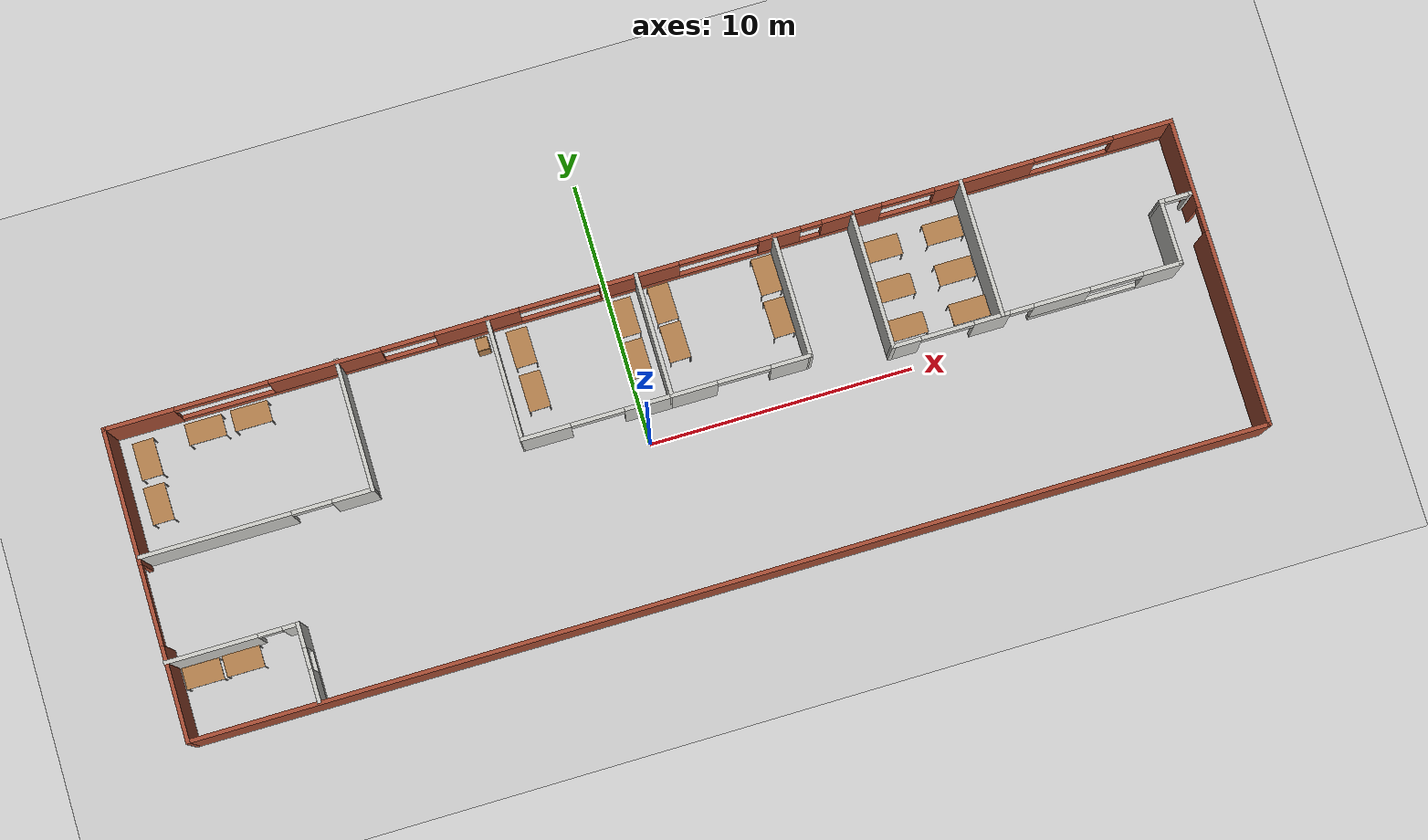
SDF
<sdf version="1.6">
 <world name="default">
  <light name="sun" type="directional">
   <pose>0 0 10 0 -0 0</pose>
   <diffuse>0.8 0.8 0.8 1</diffuse>
   <specular>0.1 0.1 0.1 1</specular>
   <attenuation>
    <range>1000</range>
    <constant>0.9</constant>
    <linear>0.01</linear>
    <quadratic>0.001</quadratic>
   </attenuation>
   <direction>-0.5 0.5 -1</direction>
  </light>
  <model name="ground_plane">
   <static>1</static>
   <link name="link">
    <collision name="collision">
     <geometry><plane><normal>0 0 1</normal><size>100 100</size></plane></geometry>
     <surface><friction><ode><mu>100</mu><mu2>50</mu2></ode></friction></surface>
    </collision>
    <visual name="visual">
     <cast_shadows>0</cast_shadows>
     <geometry><plane><normal>0 0 1</normal><size>100 100</size></plane></geometry>
     <material>
      <script><uri>file://media/materials/scripts/gazebo.material</uri><name>Gazebo/Grey</name></script>
     </material>
    </visual>
   </link>
  </model>
  <gravity>0 0 -9.8</gravity>
  <magnetic_field>6e-06 2.3e-05 -4.2e-05</magnetic_field>
  <atmosphere type="adiabatic"/>
  <physics name="default_physics" default="0" type="ode">
   <max_step_size>0.001</max_step_size>
   <real_time_factor>1</real_time_factor>
   <real_time_update_rate>1000</real_time_update_rate>
  </physics>
  <scene><ambient>0.4 0.4 0.4 1</ambient><background>0.7 0.7 0.7 1</background><shadows>1</shadows></scene>
  <spherical_coordinates>
   <surface_model>EARTH_WGS84</surface_model>
   <latitude_deg>0</latitude_deg>
   <longitude_deg>0</longitude_deg>
   <elevation>0</elevation>
   <heading_deg>0</heading_deg>
  </spherical_coordinates>
  <model name="match_5">
   <pose>1.3159 -0.064447 0 0 -0 0</pose>
   <link name="Wall_0">
    <pose>13.3885 0.676422 0 0 -0 3.14159</pose>
    <visual name="Wall_0_Visual_0">
     <pose>-4.75004 0 1.25 0 -0 0</pose>
     <geometry><box><size>1.49992 0.15 2.5</size></box></geometry>
     <material>
      <script><uri>file://media/materials/scripts/gazebo.material</uri><name>Gazebo/CeilingTiled</name></script>
      <ambient>1 1 1 1</ambient>
     </material>
    </visual>
    <collision name="Wall_0_Collision_0">
     <geometry><box><size>1.49992 0.15 2.5</size></box></geometry>
     <pose>-4.75004 0 1.25 0 -0 0</pose>
    </collision>
    <visual name="Wall_0_Visual_1">
     <pose>1.70753 0 1.25 0 -0 0</pose>
     <geometry><box><size>1.35 0.15 2.5</size></box></geometry>
     <material>
      <script><uri>file://media/materials/scripts/gazebo.material</uri><name>Gazebo/CeilingTiled</name></script>
      <ambient>1 1 1 1</ambient>
     </material>
    </visual>
    <collision name="Wall_0_Collision_1">
     <geometry><box><size>1.35 0.15 2.5</size></box></geometry>
     <pose>1.70753 0 1.25 0 -0 0</pose>
    </collision>
    <visual name="Wall_0_Visual_2">
     <pose>4.94126 0 1.25 0 -0 0</pose>
     <geometry><box><size>1.11747 0.15 2.5</size></box></geometry>
     <material>
      <script><uri>file://media/materials/scripts/gazebo.material</uri><name>Gazebo/CeilingTiled</name></script>
      <ambient>1 1 1 1</ambient>
     </material>
    </visual>
    <collision name="Wall_0_Collision_2">
     <geometry><box><size>1.11747 0.15 2.5</size></box></geometry>
     <pose>4.94126 0 1.25 0 -0 0</pose>
    </collision>
    <visual name="Wall_0_Visual_3">
     <pose>-1.93378 0 0.25 0 -0 0</pose>
     <geometry><box><size>4.13261 0.15 0.5</size></box></geometry>
     <material>
      <script><uri>file://media/materials/scripts/gazebo.material</uri><name>Gazebo/CeilingTiled</name></script>
      <ambient>1 1 1 1</ambient>
     </material>
    </visual>
    <collision name="Wall_0_Collision_3">
     <geometry><box><size>4.13261 0.15 0.5</size></box></geometry>
     <pose>-1.93378 0 0.25 0 -0 0</pose>
    </collision>
    <visual name="Wall_0_Visual_4">
     <pose>-0.933776 0 1.5 0 -0 0</pose>
     <geometry><box><size>2.13261 0.15 2</size></box></geometry>
     <material>
      <script><uri>file://media/materials/scripts/gazebo.material</uri><name>Gazebo/CeilingTiled</name></script>
      <ambient>1 1 1 1</ambient>
     </material>
    </visual>
    <collision name="Wall_0_Collision_4">
     <geometry><box><size>2.13261 0.15 2</size></box></geometry>
     <pose>-0.933776 0 1.5 0 -0 0</pose>
    </collision>
    <visual name="Wall_0_Visual_5">
     <pose>-3.00008 0 2.25 0 -0 0</pose>
     <geometry><box><size>2 0.15 0.5</size></box></geometry>
     <material>
      <script><uri>file://media/materials/scripts/gazebo.material</uri><name>Gazebo/CeilingTiled</name></script>
      <ambient>1 1 1 1</ambient>
     </material>
    </visual>
    <collision name="Wall_0_Collision_5">
     <geometry><box><size>2 0.15 0.5</size></box></geometry>
     <pose>-3.00008 0 2.25 0 -0 0</pose>
    </collision>
    <visual name="Wall_0_Visual_6">
     <pose>3.38253 0 2.25 0 -0 0</pose>
     <geometry><box><size>2 0.15 0.5</size></box></geometry>
     <material>
      <script><uri>file://media/materials/scripts/gazebo.material</uri><name>Gazebo/CeilingTiled</name></script>
      <ambient>1 1 1 1</ambient>
     </material>
    </visual>
    <collision name="Wall_0_Collision_6">
     <geometry><box><size>2 0.15 0.5</size></box></geometry>
     <pose>3.38253 0 2.25 0 -0 0</pose>
    </collision>
    <visual name="Wall_0_Visual_7">
     <pose>0.582528 0 2.25 0 -0 0</pose>
     <geometry><box><size>0.9 0.15 0.5</size></box></geometry>
     <material>
      <script><uri>file://media/materials/scripts/gazebo.material</uri><name>Gazebo/CeilingTiled</name></script>
      <ambient>1 1 1 1</ambient>
     </material>
    </visual>
    <collision name="Wall_0_Collision_7">
     <geometry><box><size>0.9 0.15 0.5</size></box></geometry>
     <pose>0.582528 0 2.25 0 -0 0</pose>
    </collision>
   </link>
   <link name="Wall_1">
    <collision name="Wall_1_Collision">
     <geometry><box><size>5.25 0.15 2.5</size></box></geometry>
     <pose>0 0 1.25 0 -0 0</pose>
    </collision>
    <visual name="Wall_1_Visual">
     <pose>0 0 1.25 0 -0 0</pose>
     <geometry><box><size>5.25 0.15 2.5</size></box></geometry>
     <material>
      <script><uri>file://media/materials/scripts/gazebo.material</uri><name>Gazebo/CeilingTiled</name></script>
      <ambient>1 1 1 1</ambient>
     </material>
    </visual>
    <pose>7.96355 3.22642 0 0 -0 1.5708</pose>
   </link>
   <link name="Wall_11">
    <pose>-6.03645 5.77642 0 0 -0 0</pose>
    <visual name="Wall_11_Visual_0">
     <pose>-12.7347 0 1.25 0 -0 0</pose>
     <geometry><box><size>2.68052 0.15 2.5</size></box></geometry>
     <material>
      <script><uri>file://media/materials/scripts/gazebo.material</uri><name>Gazebo/Bricks</name></script>
      <ambient>1 1 1 1</ambient>
     </material>
    </visual>
    <collision name="Wall_11_Collision_0">
     <geometry><box><size>2.68052 0.15 2.5</size></box></geometry>
     <pose>-12.7347 0 1.25 0 -0 0</pose>
    </collision>
    <visual name="Wall_11_Visual_1">
     <pose>1.34026 0 0.25 0 -0 0</pose>
     <geometry><box><size>25.4695 0.15 0.5</size></box></geometry>
     <material>
      <script><uri>file://media/materials/scripts/gazebo.material</uri><name>Gazebo/Bricks</name></script>
      <ambient>1 1 1 1</ambient>
     </material>
    </visual>
    <collision name="Wall_11_Collision_1">
     <geometry><box><size>25.4695 0.15 0.5</size></box></geometry>
     <pose>1.34026 0 0.25 0 -0 0</pose>
    </collision>
    <visual name="Wall_11_Visual_2">
     <pose>-5.79992 0 1.5 0 -0 0</pose>
     <geometry><box><size>4.18913 0.15 2</size></box></geometry>
     <material>
      <script><uri>file://media/materials/scripts/gazebo.material</uri><name>Gazebo/Bricks</name></script>
      <ambient>1 1 1 1</ambient>
     </material>
    </visual>
    <collision name="Wall_11_Collision_2">
     <geometry><box><size>4.18913 0.15 2</size></box></geometry>
     <pose>-5.79992 0 1.5 0 -0 0</pose>
    </collision>
    <visual name="Wall_11_Visual_3">
     <pose>-0.120572 0 1.5 0 -0 0</pose>
     <geometry><box><size>3.16956 0.15 2</size></box></geometry>
     <material>
      <script><uri>file://media/materials/scripts/gazebo.material</uri><name>Gazebo/Bricks</name></script>
      <ambient>1 1 1 1</ambient>
     </material>
    </visual>
    <collision name="Wall_11_Collision_3">
     <geometry><box><size>3.16956 0.15 2</size></box></geometry>
     <pose>-0.120572 0 1.5 0 -0 0</pose>
    </collision>
    <visual name="Wall_11_Visual_4">
     <pose>5.96421 0 1.5 0 -0 0</pose>
     <geometry><box><size>3 0.15 2</size></box></geometry>
     <material>
      <script><uri>file://media/materials/scripts/gazebo.material</uri><name>Gazebo/Bricks</name></script>
      <ambient>1 1 1 1</ambient>
     </material>
    </visual>
    <collision name="Wall_11_Collision_4">
     <geometry><box><size>3 0.15 2</size></box></geometry>
     <pose>5.96421 0 1.5 0 -0 0</pose>
    </collision>
    <visual name="Wall_11_Visual_5">
     <pose>11.2533 0 1.5 0 -0 0</pose>
     <geometry><box><size>1.57826 0.15 2</size></box></geometry>
     <material>
      <script><uri>file://media/materials/scripts/gazebo.material</uri><name>Gazebo/Bricks</name></script>
      <ambient>1 1 1 1</ambient>
     </material>
    </visual>
    <collision name="Wall_11_Collision_5">
     <geometry><box><size>1.57826 0.15 2</size></box></geometry>
     <pose>11.2533 0 1.5 0 -0 0</pose>
    </collision>
    <visual name="Wall_11_Visual_6">
     <pose>13.4587 0 1.5 0 -0 0</pose>
     <geometry><box><size>1.23253 0.15 2</size></box></geometry>
     <material>
      <script><uri>file://media/materials/scripts/gazebo.material</uri><name>Gazebo/Bricks</name></script>
      <ambient>1 1 1 1</ambient>
     </material>
    </visual>
    <collision name="Wall_11_Collision_6">
     <geometry><box><size>1.23253 0.15 2</size></box></geometry>
     <pose>13.4587 0 1.5 0 -0 0</pose>
    </collision>
    <visual name="Wall_11_Visual_7">
     <pose>-9.64448 0 2.25 0 -0 0</pose>
     <geometry><box><size>3.5 0.15 0.5</size></box></geometry>
     <material>
      <script><uri>file://media/materials/scripts/gazebo.material</uri><name>Gazebo/Bricks</name></script>
      <ambient>1 1 1 1</ambient>
     </material>
    </visual>
    <collision name="Wall_11_Collision_7">
     <geometry><box><size>3.5 0.15 0.5</size></box></geometry>
     <pose>-9.64448 0 2.25 0 -0 0</pose>
    </collision>
    <visual name="Wall_11_Visual_8">
     <pose>-2.70535 0 2.25 0 -0 0</pose>
     <geometry><box><size>2 0.15 0.5</size></box></geometry>
     <material>
      <script><uri>file://media/materials/scripts/gazebo.material</uri><name>Gazebo/Bricks</name></script>
      <ambient>1 1 1 1</ambient>
     </material>
    </visual>
    <collision name="Wall_11_Collision_8">
     <geometry><box><size>2 0.15 0.5</size></box></geometry>
     <pose>-2.70535 0 2.25 0 -0 0</pose>
    </collision>
    <visual name="Wall_11_Visual_9">
     <pose>2.96421 0 2.25 0 -0 0</pose>
     <geometry><box><size>3 0.15 0.5</size></box></geometry>
     <material>
      <script><uri>file://media/materials/scripts/gazebo.material</uri><name>Gazebo/Bricks</name></script>
      <ambient>1 1 1 1</ambient>
     </material>
    </visual>
    <collision name="Wall_11_Collision_9">
     <geometry><box><size>3 0.15 0.5</size></box></geometry>
     <pose>2.96421 0 2.25 0 -0 0</pose>
    </collision>
    <visual name="Wall_11_Visual_10">
     <pose>8.96421 0 2.25 0 -0 0</pose>
     <geometry><box><size>3 0.15 0.5</size></box></geometry>
     <material>
      <script><uri>file://media/materials/scripts/gazebo.material</uri><name>Gazebo/Bricks</name></script>
      <ambient>1 1 1 1</ambient>
     </material>
    </visual>
    <collision name="Wall_11_Collision_10">
     <geometry><box><size>3 0.15 0.5</size></box></geometry>
     <pose>8.96421 0 2.25 0 -0 0</pose>
    </collision>
    <visual name="Wall_11_Visual_11">
     <pose>12.4425 0 2.25 0 -0 0</pose>
     <geometry><box><size>0.8 0.15 0.5</size></box></geometry>
     <material>
      <script><uri>file://media/materials/scripts/gazebo.material</uri><name>Gazebo/Bricks</name></script>
      <ambient>1 1 1 1</ambient>
     </material>
    </visual>
    <collision name="Wall_11_Collision_11">
     <geometry><box><size>0.8 0.15 0.5</size></box></geometry>
     <pose>12.4425 0 2.25 0 -0 0</pose>
    </collision>
   </link>
   <link name="Wall_13">
    <collision name="Wall_13_Collision">
     <geometry><box><size>5 0.15 2.5</size></box></geometry>
     <pose>0 0 1.25 0 -0 0</pose>
    </collision>
    <visual name="Wall_13_Visual">
     <pose>0 0 1.25 0 -0 0</pose>
     <geometry><box><size>5 0.15 2.5</size></box></geometry>
     <material>
      <script><uri>file://media/materials/scripts/gazebo.material</uri><name>Gazebo/CeilingTiled</name></script>
      <ambient>1 1 1 1</ambient>
     </material>
    </visual>
    <pose>-11.3817 3.39858 0 0 0 -1.5708</pose>
   </link>
   <link name="Wall_14">
    <pose>-15.6817 0.973578 0 0 -0 3.14159</pose>
    <visual name="Wall_14_Visual_0">
     <pose>-3.58899 0 1.25 0 -0 0</pose>
     <geometry><box><size>1.57202 0.15 2.5</size></box></geometry>
     <material>
      <script><uri>file://media/materials/scripts/gazebo.material</uri><name>Gazebo/CeilingTiled</name></script>
      <ambient>1 1 1 1</ambient>
     </material>
    </visual>
    <collision name="Wall_14_Collision_0">
     <geometry><box><size>1.57202 0.15 2.5</size></box></geometry>
     <pose>-3.58899 0 1.25 0 -0 0</pose>
    </collision>
    <visual name="Wall_14_Visual_1">
     <pose>1.53601 0 1.25 0 -0 0</pose>
     <geometry><box><size>5.67798 0.15 2.5</size></box></geometry>
     <material>
      <script><uri>file://media/materials/scripts/gazebo.material</uri><name>Gazebo/CeilingTiled</name></script>
      <ambient>1 1 1 1</ambient>
     </material>
    </visual>
    <collision name="Wall_14_Collision_1">
     <geometry><box><size>5.67798 0.15 2.5</size></box></geometry>
     <pose>1.53601 0 1.25 0 -0 0</pose>
    </collision>
    <visual name="Wall_14_Visual_2">
     <pose>-2.05298 0 2.25 0 -0 0</pose>
     <geometry><box><size>1.5 0.15 0.5</size></box></geometry>
     <material>
      <script><uri>file://media/materials/scripts/gazebo.material</uri><name>Gazebo/CeilingTiled</name></script>
      <ambient>1 1 1 1</ambient>
     </material>
    </visual>
    <collision name="Wall_14_Collision_2">
     <geometry><box><size>1.5 0.15 0.5</size></box></geometry>
     <pose>-2.05298 0 2.25 0 -0 0</pose>
    </collision>
   </link>
   <link name="Wall_17">
    <pose>-2.97277 1.20854 0 0 -0 0</pose>
    <visual name="Wall_17_Visual_0">
     <pose>-1.92637 0 1.25 0 -0 0</pose>
     <geometry><box><size>1.89726 0.15 2.5</size></box></geometry>
     <material>
      <script><uri>file://media/materials/scripts/gazebo.material</uri><name>Gazebo/CeilingTiled</name></script>
      <ambient>1 1 1 1</ambient>
     </material>
    </visual>
    <collision name="Wall_17_Collision_0">
     <geometry><box><size>1.89726 0.15 2.5</size></box></geometry>
     <pose>-1.92637 0 1.25 0 -0 0</pose>
    </collision>
    <visual name="Wall_17_Visual_1">
     <pose>1.94863 0 1.25 0 -0 0</pose>
     <geometry><box><size>1.85274 0.15 2.5</size></box></geometry>
     <material>
      <script><uri>file://media/materials/scripts/gazebo.material</uri><name>Gazebo/CeilingTiled</name></script>
      <ambient>1 1 1 1</ambient>
     </material>
    </visual>
    <collision name="Wall_17_Collision_1">
     <geometry><box><size>1.85274 0.15 2.5</size></box></geometry>
     <pose>1.94863 0 1.25 0 -0 0</pose>
    </collision>
    <visual name="Wall_17_Visual_2">
     <pose>0.022262 0 2.25 0 -0 0</pose>
     <geometry><box><size>2 0.15 0.5</size></box></geometry>
     <material>
      <script><uri>file://media/materials/scripts/gazebo.material</uri><name>Gazebo/CeilingTiled</name></script>
      <ambient>1 1 1 1</ambient>
     </material>
    </visual>
    <collision name="Wall_17_Collision_2">
     <geometry><box><size>2 0.15 0.5</size></box></geometry>
     <pose>0.022262 0 2.25 0 -0 0</pose>
    </collision>
   </link>
   <link name="Wall_18">
    <collision name="Wall_18_Collision">
     <geometry><box><size>4.75 0.15 2.5</size></box></geometry>
     <pose>0 0 1.25 0 -0 0</pose>
    </collision>
    <visual name="Wall_18_Visual">
     <pose>0 0 1.25 0 -0 0</pose>
     <geometry><box><size>4.75 0.15 2.5</size></box></geometry>
     <material>
      <script><uri>file://media/materials/scripts/gazebo.material</uri><name>Gazebo/CeilingTiled</name></script>
      <ambient>1 1 1 1</ambient>
     </material>
    </visual>
    <pose>-0.172766 3.50854 0 0 -0 1.5708</pose>
   </link>
   <link name="Wall_2">
    <pose>14.0135 5.77642 0 0 -0 0</pose>
    <visual name="Wall_2_Visual_0">
     <pose>-5.53148 0 1.25 0 -0 0</pose>
     <geometry><box><size>1.18704 0.15 2.5</size></box></geometry>
     <material>
      <script><uri>file://media/materials/scripts/gazebo.material</uri><name>Gazebo/Bricks</name></script>
      <ambient>1 1 1 1</ambient>
     </material>
    </visual>
    <collision name="Wall_2_Collision_0">
     <geometry><box><size>1.18704 0.15 2.5</size></box></geometry>
     <pose>-5.53148 0 1.25 0 -0 0</pose>
    </collision>
    <visual name="Wall_2_Visual_1">
     <pose>0.593519 0 0.25 0 -0 0</pose>
     <geometry><box><size>11.063 0.15 0.5</size></box></geometry>
     <material>
      <script><uri>file://media/materials/scripts/gazebo.material</uri><name>Gazebo/Bricks</name></script>
      <ambient>1 1 1 1</ambient>
     </material>
    </visual>
    <collision name="Wall_2_Collision_1">
     <geometry><box><size>11.063 0.15 0.5</size></box></geometry>
     <pose>0.593519 0 0.25 0 -0 0</pose>
    </collision>
    <visual name="Wall_2_Visual_2">
     <pose>-1.04883 0 1.5 0 -0 0</pose>
     <geometry><box><size>3.77826 0.15 2</size></box></geometry>
     <material>
      <script><uri>file://media/materials/scripts/gazebo.material</uri><name>Gazebo/Bricks</name></script>
      <ambient>1 1 1 1</ambient>
     </material>
    </visual>
    <collision name="Wall_2_Collision_2">
     <geometry><box><size>3.77826 0.15 2</size></box></geometry>
     <pose>-1.04883 0 1.5 0 -0 0</pose>
    </collision>
    <visual name="Wall_2_Visual_3">
     <pose>4.98265 0 1.5 0 -0 0</pose>
     <geometry><box><size>2.2847 0.15 2</size></box></geometry>
     <material>
      <script><uri>file://media/materials/scripts/gazebo.material</uri><name>Gazebo/Bricks</name></script>
      <ambient>1 1 1 1</ambient>
     </material>
    </visual>
    <collision name="Wall_2_Collision_3">
     <geometry><box><size>2.2847 0.15 2</size></box></geometry>
     <pose>4.98265 0 1.5 0 -0 0</pose>
    </collision>
    <visual name="Wall_2_Visual_4">
     <pose>-3.93796 0 2.25 0 -0 0</pose>
     <geometry><box><size>2 0.15 0.5</size></box></geometry>
     <material>
      <script><uri>file://media/materials/scripts/gazebo.material</uri><name>Gazebo/Bricks</name></script>
      <ambient>1 1 1 1</ambient>
     </material>
    </visual>
    <collision name="Wall_2_Collision_4">
     <geometry><box><size>2 0.15 0.5</size></box></geometry>
     <pose>-3.93796 0 2.25 0 -0 0</pose>
    </collision>
    <visual name="Wall_2_Visual_5">
     <pose>2.3403 0 2.25 0 -0 0</pose>
     <geometry><box><size>3 0.15 0.5</size></box></geometry>
     <material>
      <script><uri>file://media/materials/scripts/gazebo.material</uri><name>Gazebo/Bricks</name></script>
      <ambient>1 1 1 1</ambient>
     </material>
    </visual>
    <collision name="Wall_2_Collision_5">
     <geometry><box><size>3 0.15 0.5</size></box></geometry>
     <pose>2.3403 0 2.25 0 -0 0</pose>
    </collision>
   </link>
   <link name="Wall_22">
    <collision name="Wall_22_Collision">
     <geometry><box><size>2.5 0.15 2.5</size></box></geometry>
     <pose>0 0 1.25 0 -0 0</pose>
    </collision>
    <visual name="Wall_22_Visual">
     <pose>0 0 1.25 0 -0 0</pose>
     <geometry><box><size>2.5 0.15 2.5</size></box></geometry>
     <material>
      <script><uri>file://media/materials/scripts/gazebo.material</uri><name>Gazebo/CeilingTiled</name></script>
      <ambient>1 1 1 1</ambient>
     </material>
    </visual>
    <pose>18.8135 1.85142 0 0 -0 1.5708</pose>
   </link>
   <link name="Wall_23">
    <pose>19.3635 3.02642 0 0 -0 0</pose>
    <visual name="Wall_23_Visual_0">
     <pose>-0.520611 0 1.25 0 -0 0</pose>
     <geometry><box><size>0.208777 0.15 2.5</size></box></geometry>
     <material>
      <script><uri>file://media/materials/scripts/gazebo.material</uri><name>Gazebo/CeilingTiled</name></script>
      <ambient>1 1 1 1</ambient>
     </material>
    </visual>
    <collision name="Wall_23_Collision_0">
     <geometry><box><size>0.208777 0.15 2.5</size></box></geometry>
     <pose>-0.520611 0 1.25 0 -0 0</pose>
    </collision>
    <visual name="Wall_23_Visual_1">
     <pose>0.554389 0 1.25 0 -0 0</pose>
     <geometry><box><size>0.141223 0.15 2.5</size></box></geometry>
     <material>
      <script><uri>file://media/materials/scripts/gazebo.material</uri><name>Gazebo/CeilingTiled</name></script>
      <ambient>1 1 1 1</ambient>
     </material>
    </visual>
    <collision name="Wall_23_Collision_1">
     <geometry><box><size>0.141223 0.15 2.5</size></box></geometry>
     <pose>0.554389 0 1.25 0 -0 0</pose>
    </collision>
    <visual name="Wall_23_Visual_2">
     <pose>0.033777 0 2.25 0 -0 0</pose>
     <geometry><box><size>0.9 0.15 0.5</size></box></geometry>
     <material>
      <script><uri>file://media/materials/scripts/gazebo.material</uri><name>Gazebo/CeilingTiled</name></script>
      <ambient>1 1 1 1</ambient>
     </material>
    </visual>
    <collision name="Wall_23_Collision_2">
     <geometry><box><size>0.9 0.15 0.5</size></box></geometry>
     <pose>0.033777 0 2.25 0 -0 0</pose>
    </collision>
   </link>
   <link name="Wall_27">
    <collision name="Wall_27_Collision">
     <geometry><box><size>4.75 0.15 2.5</size></box></geometry>
     <pose>0 0 1.25 0 -0 0</pose>
    </collision>
    <visual name="Wall_27_Visual">
     <pose>0 0 1.25 0 -0 0</pose>
     <geometry><box><size>4.75 0.15 2.5</size></box></geometry>
     <material>
      <script><uri>file://media/materials/scripts/gazebo.material</uri><name>Gazebo/CeilingTiled</name></script>
      <ambient>1 1 1 1</ambient>
     </material>
    </visual>
    <pose>-5.77277 3.50854 0 0 -0 1.5708</pose>
   </link>
   <link name="Wall_29">
    <collision name="Wall_29_Collision">
     <geometry><box><size>5.25 0.15 2.5</size></box></geometry>
     <pose>0 0 1.25 0 -0 0</pose>
    </collision>
    <visual name="Wall_29_Visual">
     <pose>0 0 1.25 0 -0 0</pose>
     <geometry><box><size>5.25 0.15 2.5</size></box></geometry>
     <material>
      <script><uri>file://media/materials/scripts/gazebo.material</uri><name>Gazebo/CeilingTiled</name></script>
      <ambient>1 1 1 1</ambient>
     </material>
    </visual>
    <pose>12.0775 3.23316 0 0 -0 1.5708</pose>
   </link>
   <link name="Wall_3">
    <pose>20.0635 -0.023578 0 0 0 -1.5708</pose>
    <visual name="Wall_3_Visual_0">
     <pose>-4.16442 0 1.25 0 -0 0</pose>
     <geometry><box><size>3.42116 0.15 2.5</size></box></geometry>
     <material>
      <script><uri>file://media/materials/scripts/gazebo.material</uri><name>Gazebo/Bricks</name></script>
      <ambient>1 1 1 1</ambient>
     </material>
    </visual>
    <collision name="Wall_3_Collision_0">
     <geometry><box><size>3.42116 0.15 2.5</size></box></geometry>
     <pose>-4.16442 0 1.25 0 -0 0</pose>
    </collision>
    <visual name="Wall_3_Visual_1">
     <pose>2.16058 0 1.25 0 -0 0</pose>
     <geometry><box><size>7.42884 0.15 2.5</size></box></geometry>
     <material>
      <script><uri>file://media/materials/scripts/gazebo.material</uri><name>Gazebo/Bricks</name></script>
      <ambient>1 1 1 1</ambient>
     </material>
    </visual>
    <collision name="Wall_3_Collision_1">
     <geometry><box><size>7.42884 0.15 2.5</size></box></geometry>
     <pose>2.16058 0 1.25 0 -0 0</pose>
    </collision>
    <visual name="Wall_3_Visual_2">
     <pose>-2.00384 0 2.25 0 -0 0</pose>
     <geometry><box><size>0.9 0.15 0.5</size></box></geometry>
     <material>
      <script><uri>file://media/materials/scripts/gazebo.material</uri><name>Gazebo/Bricks</name></script>
      <ambient>1 1 1 1</ambient>
     </material>
    </visual>
    <collision name="Wall_3_Collision_2">
     <geometry><box><size>0.9 0.15 0.5</size></box></geometry>
     <pose>-2.00384 0 2.25 0 -0 0</pose>
    </collision>
   </link>
   <link name="Wall_31">
    <pose>-17.6385 -2.9067 0 0 -0 0</pose>
    <visual name="Wall_31_Visual_0">
     <pose>-0.774457 0 1.25 0 -0 0</pose>
     <geometry><box><size>3.45109 0.15 2.5</size></box></geometry>
     <material>
      <script><uri>file://media/materials/scripts/gazebo.material</uri><name>Gazebo/CeilingTiled</name></script>
      <ambient>1 1 1 1</ambient>
     </material>
    </visual>
    <collision name="Wall_31_Collision_0">
     <geometry><box><size>3.45109 0.15 2.5</size></box></geometry>
     <pose>-0.774457 0 1.25 0 -0 0</pose>
    </collision>
    <visual name="Wall_31_Visual_1">
     <pose>2.17554 0 1.25 0 -0 0</pose>
     <geometry><box><size>0.648913 0.15 2.5</size></box></geometry>
     <material>
      <script><uri>file://media/materials/scripts/gazebo.material</uri><name>Gazebo/CeilingTiled</name></script>
      <ambient>1 1 1 1</ambient>
     </material>
    </visual>
    <collision name="Wall_31_Collision_1">
     <geometry><box><size>0.648913 0.15 2.5</size></box></geometry>
     <pose>2.17554 0 1.25 0 -0 0</pose>
    </collision>
    <visual name="Wall_31_Visual_2">
     <pose>1.40109 0 2.25 0 -0 0</pose>
     <geometry><box><size>0.9 0.15 0.5</size></box></geometry>
     <material>
      <script><uri>file://media/materials/scripts/gazebo.material</uri><name>Gazebo/CeilingTiled</name></script>
      <ambient>1 1 1 1</ambient>
     </material>
    </visual>
    <collision name="Wall_31_Collision_2">
     <geometry><box><size>0.9 0.15 0.5</size></box></geometry>
     <pose>1.40109 0 2.25 0 -0 0</pose>
    </collision>
   </link>
   <link name="Wall_32">
    <pose>-15.2135 -4.3317 0 0 0 -1.5708</pose>
    <visual name="Wall_32_Visual_0">
     <pose>-1.02772 0 1.25 0 -0 0</pose>
     <geometry><box><size>0.944565 0.15 2.5</size></box></geometry>
     <material>
      <script><uri>file://media/materials/scripts/gazebo.material</uri><name>Gazebo/CeilingTiled</name></script>
      <ambient>1 1 1 1</ambient>
     </material>
    </visual>
    <collision name="Wall_32_Collision_0">
     <geometry><box><size>0.944565 0.15 2.5</size></box></geometry>
     <pose>-1.02772 0 1.25 0 -0 0</pose>
    </collision>
    <visual name="Wall_32_Visual_1">
     <pose>0.472283 0 0.25 0 -0 0</pose>
     <geometry><box><size>2.05544 0.15 0.5</size></box></geometry>
     <material>
      <script><uri>file://media/materials/scripts/gazebo.material</uri><name>Gazebo/CeilingTiled</name></script>
      <ambient>1 1 1 1</ambient>
     </material>
    </visual>
    <collision name="Wall_32_Collision_1">
     <geometry><box><size>2.05544 0.15 0.5</size></box></geometry>
     <pose>0.472283 0 0.25 0 -0 0</pose>
    </collision>
    <visual name="Wall_32_Visual_2">
     <pose>0.872283 0 1.5 0 -0 0</pose>
     <geometry><box><size>1.25544 0.15 2</size></box></geometry>
     <material>
      <script><uri>file://media/materials/scripts/gazebo.material</uri><name>Gazebo/CeilingTiled</name></script>
      <ambient>1 1 1 1</ambient>
     </material>
    </visual>
    <collision name="Wall_32_Collision_2">
     <geometry><box><size>1.25544 0.15 2</size></box></geometry>
     <pose>0.872283 0 1.5 0 -0 0</pose>
    </collision>
    <visual name="Wall_32_Visual_3">
     <pose>-0.155435 0 2.25 0 -0 0</pose>
     <geometry><box><size>0.8 0.15 0.5</size></box></geometry>
     <material>
      <script><uri>file://media/materials/scripts/gazebo.material</uri><name>Gazebo/CeilingTiled</name></script>
      <ambient>1 1 1 1</ambient>
     </material>
    </visual>
    <collision name="Wall_32_Collision_3">
     <geometry><box><size>0.8 0.15 0.5</size></box></geometry>
     <pose>-0.155435 0 2.25 0 -0 0</pose>
    </collision>
   </link>
   <link name="Wall_36">
    <collision name="Wall_36_Collision">
     <geometry><box><size>4.75 0.15 2.5</size></box></geometry>
     <pose>0 0 1.25 0 -0 0</pose>
    </collision>
    <visual name="Wall_36_Visual">
     <pose>0 0 1.25 0 -0 0</pose>
     <geometry><box><size>4.75 0.15 2.5</size></box></geometry>
     <material>
      <script><uri>file://media/materials/scripts/gazebo.material</uri><name>Gazebo/CeilingTiled</name></script>
      <ambient>1 1 1 1</ambient>
     </material>
    </visual>
    <pose>5.01689 3.50635 0 0 -0 1.5708</pose>
   </link>
   <link name="Wall_4">
    <collision name="Wall_4_Collision">
     <geometry><box><size>40.25 0.15 2.5</size></box></geometry>
     <pose>0 0 1.25 0 -0 0</pose>
    </collision>
    <visual name="Wall_4_Visual">
     <pose>0 0 1.25 0 -0 0</pose>
     <geometry><box><size>40.25 0.15 2.5</size></box></geometry>
     <material>
      <script><uri>file://media/materials/scripts/gazebo.material</uri><name>Gazebo/Bricks</name></script>
      <ambient>1 1 1 1</ambient>
     </material>
    </visual>
    <pose>0.013546 -5.82358 0 0 -0 3.14159</pose>
   </link>
   <link name="Wall_40">
    <pose>2.42206 1.20744 0 0 0 -0.000423</pose>
    <visual name="Wall_40_Visual_0">
     <pose>-1.78205 0 1.25 0 -0 0</pose>
     <geometry><box><size>1.77556 0.15 2.5</size></box></geometry>
     <material>
      <script><uri>file://media/materials/scripts/gazebo.material</uri><name>Gazebo/CeilingTiled</name></script>
      <ambient>1 1 1 1</ambient>
     </material>
    </visual>
    <collision name="Wall_40_Collision_0">
     <geometry><box><size>1.77556 0.15 2.5</size></box></geometry>
     <pose>-1.78205 0 1.25 0 -0 0</pose>
    </collision>
    <visual name="Wall_40_Visual_1">
     <pose>1.88778 0 1.25 0 -0 0</pose>
     <geometry><box><size>1.56409 0.15 2.5</size></box></geometry>
     <material>
      <script><uri>file://media/materials/scripts/gazebo.material</uri><name>Gazebo/CeilingTiled</name></script>
      <ambient>1 1 1 1</ambient>
     </material>
    </visual>
    <collision name="Wall_40_Collision_1">
     <geometry><box><size>1.56409 0.15 2.5</size></box></geometry>
     <pose>1.88778 0 1.25 0 -0 0</pose>
    </collision>
    <visual name="Wall_40_Visual_2">
     <pose>0.105737 0 2.25 0 -0 0</pose>
     <geometry><box><size>2 0.15 0.5</size></box></geometry>
     <material>
      <script><uri>file://media/materials/scripts/gazebo.material</uri><name>Gazebo/CeilingTiled</name></script>
      <ambient>1 1 1 1</ambient>
     </material>
    </visual>
    <collision name="Wall_40_Collision_2">
     <geometry><box><size>2 0.15 0.5</size></box></geometry>
     <pose>0.105737 0 2.25 0 -0 0</pose>
    </collision>
   </link>
   <link name="Wall_9">
    <pose>-20.0365 -0.023578 0 0 -0 1.5708</pose>
    <visual name="Wall_9_Visual_0">
     <pose>-4.07689 0 1.25 0 -0 0</pose>
     <geometry><box><size>3.59623 0.15 2.5</size></box></geometry>
     <material>
      <script><uri>file://media/materials/scripts/gazebo.material</uri><name>Gazebo/Bricks</name></script>
      <ambient>1 1 1 1</ambient>
     </material>
    </visual>
    <collision name="Wall_9_Collision_0">
     <geometry><box><size>3.59623 0.15 2.5</size></box></geometry>
     <pose>-4.07689 0 1.25 0 -0 0</pose>
    </collision>
    <visual name="Wall_9_Visual_1">
     <pose>3.29811 0 1.25 0 -0 0</pose>
     <geometry><box><size>5.15377 0.15 2.5</size></box></geometry>
     <material>
      <script><uri>file://media/materials/scripts/gazebo.material</uri><name>Gazebo/Bricks</name></script>
      <ambient>1 1 1 1</ambient>
     </material>
    </visual>
    <collision name="Wall_9_Collision_1">
     <geometry><box><size>5.15377 0.15 2.5</size></box></geometry>
     <pose>3.29811 0 1.25 0 -0 0</pose>
    </collision>
    <visual name="Wall_9_Visual_2">
     <pose>-0.778773 0 2.25 0 -0 0</pose>
     <geometry><box><size>3 0.15 0.5</size></box></geometry>
     <material>
      <script><uri>file://media/materials/scripts/gazebo.material</uri><name>Gazebo/Bricks</name></script>
      <ambient>1 1 1 1</ambient>
     </material>
    </visual>
    <collision name="Wall_9_Collision_2">
     <geometry><box><size>3 0.15 0.5</size></box></geometry>
     <pose>-0.778773 0 2.25 0 -0 0</pose>
    </collision>
   </link>
   <static>1</static>
  </model>
  <model name="table">
   <static>0</static>
   <link name="link">
    <collision name="surface">
     <pose>0 0 1 0 -0 0</pose>
     <geometry><box><size>1.5 0.8 0.03</size></box></geometry>
     <surface><friction><ode><mu>0.6</mu><mu2>0.6</mu2></ode></friction></surface>
    </collision>
    <visual name="visual1">
     <pose>0 0 1 0 -0 0</pose>
     <geometry><box><size>1.4 0.8 0.04</size></box></geometry>
     <material>
      <script><uri>file://media/materials/scripts/gazebo.material</uri><name>Gazebo/Wood</name></script>
     </material>
    </visual>
    <collision name="front_left_leg">
     <pose>0.68 0.38 0.5 0 -0 0</pose>
     <geometry><cylinder><radius>0.02</radius><length>1</length></cylinder></geometry>
    </collision>
    <visual name="front_left_leg">
     <pose>0.68 0.38 0.5 0 -0 0</pose>
     <geometry><cylinder><radius>0.02</radius><length>1</length></cylinder></geometry>
     <material>
      <script><uri>file://media/materials/scripts/gazebo.material</uri><name>Gazebo/Grey</name></script>
     </material>
    </visual>
    <collision name="front_right_leg">
     <pose>0.68 -0.38 0.5 0 -0 0</pose>
     <geometry><cylinder><radius>0.02</radius><length>1</length></cylinder></geometry>
    </collision>
    <visual name="front_right_leg">
     <pose>0.68 -0.38 0.5 0 -0 0</pose>
     <geometry><cylinder><radius>0.02</radius><length>1</length></cylinder></geometry>
     <material>
      <script><uri>file://media/materials/scripts/gazebo.material</uri><name>Gazebo/Grey</name></script>
     </material>
    </visual>
    <collision name="back_right_leg">
     <pose>-0.68 -0.38 0.5 0 -0 0</pose>
     <geometry><cylinder><radius>0.02</radius><length>1</length></cylinder></geometry>
    </collision>
    <visual name="back_right_leg">
     <pose>-0.68 -0.38 0.5 0 -0 0</pose>
     <geometry><cylinder><radius>0.02</radius><length>1</length></cylinder></geometry>
     <material>
      <script><uri>file://media/materials/scripts/gazebo.material</uri><name>Gazebo/Grey</name></script>
     </material>
    </visual>
    <collision name="back_left_leg">
     <pose>-0.68 0.38 0.5 0 -0 0</pose>
     <geometry><cylinder><radius>0.02</radius><length>1</length></cylinder></geometry>
    </collision>
    <visual name="back_left_leg">
     <pose>-0.68 0.38 0.5 0 -0 0</pose>
     <geometry><cylinder><radius>0.02</radius><length>1</length></cylinder></geometry>
     <material>
      <script><uri>file://media/materials/scripts/gazebo.material</uri><name>Gazebo/Grey</name></script>
     </material>
    </visual>
    <inertial>
     <inertia><ixx>1</ixx><ixy>0</ixy><ixz>0</ixz><iyy>1</iyy><iyz>0</iyz><izz>1</izz></inertia>
     <mass>1</mass>
    </inertial>
   </link>
   <pose>12.4431 4.43763 -1e-06 0 1e-06 0</pose>
  </model>
  <model name="table_clone">
   <static>0</static>
   <link name="link">
    <collision name="surface">
     <pose>0 0 1 0 -0 0</pose>
     <geometry><box><size>1.5 0.8 0.03</size></box></geometry>
     <surface><friction><ode><mu>0.6</mu><mu2>0.6</mu2></ode></friction></surface>
    </collision>
    <visual name="visual1">
     <pose>0 0 1 0 -0 0</pose>
     <geometry><box><size>1.4 0.8 0.04</size></box></geometry>
     <material>
      <script><uri>file://media/materials/scripts/gazebo.material</uri><name>Gazebo/Wood</name></script>
     </material>
    </visual>
    <collision name="front_left_leg">
     <pose>0.68 0.38 0.5 0 -0 0</pose>
     <geometry><cylinder><radius>0.02</radius><length>1</length></cylinder></geometry>
    </collision>
    <visual name="front_left_leg">
     <pose>0.68 0.38 0.5 0 -0 0</pose>
     <geometry><cylinder><radius>0.02</radius><length>1</length></cylinder></geometry>
     <material>
      <script><uri>file://media/materials/scripts/gazebo.material</uri><name>Gazebo/Grey</name></script>
     </material>
    </visual>
    <collision name="front_right_leg">
     <pose>0.68 -0.38 0.5 0 -0 0</pose>
     <geometry><cylinder><radius>0.02</radius><length>1</length></cylinder></geometry>
    </collision>
    <visual name="front_right_leg">
     <pose>0.68 -0.38 0.5 0 -0 0</pose>
     <geometry><cylinder><radius>0.02</radius><length>1</length></cylinder></geometry>
     <material>
      <script><uri>file://media/materials/scripts/gazebo.material</uri><name>Gazebo/Grey</name></script>
     </material>
    </visual>
    <collision name="back_right_leg">
     <pose>-0.68 -0.38 0.5 0 -0 0</pose>
     <geometry><cylinder><radius>0.02</radius><length>1</length></cylinder></geometry>
    </collision>
    <visual name="back_right_leg">
     <pose>-0.68 -0.38 0.5 0 -0 0</pose>
     <geometry><cylinder><radius>0.02</radius><length>1</length></cylinder></geometry>
     <material>
      <script><uri>file://media/materials/scripts/gazebo.material</uri><name>Gazebo/Grey</name></script>
     </material>
    </visual>
    <collision name="back_left_leg">
     <pose>-0.68 0.38 0.5 0 -0 0</pose>
     <geometry><cylinder><radius>0.02</radius><length>1</length></cylinder></geometry>
    </collision>
    <visual name="back_left_leg">
     <pose>-0.68 0.38 0.5 0 -0 0</pose>
     <geometry><cylinder><radius>0.02</radius><length>1</length></cylinder></geometry>
     <material>
      <script><uri>file://media/materials/scripts/gazebo.material</uri><name>Gazebo/Grey</name></script>
     </material>
    </visual>
    <inertial>
     <inertia><ixx>1</ixx><ixy>0</ixy><ixz>0</ixz><iyy>1</iyy><iyz>0</iyz><izz>1</izz></inertia>
     <mass>1</mass>
    </inertial>
   </link>
   <pose>12.4409 2.87344 -6e-06 2e-06 -5e-06 -0</pose>
  </model>
  <model name="table_clone_0">
   <static>0</static>
   <link name="link">
    <collision name="surface">
     <pose>0 0 1 0 -0 0</pose>
     <geometry><box><size>1.5 0.8 0.03</size></box></geometry>
     <surface><friction><ode><mu>0.6</mu><mu2>0.6</mu2></ode></friction></surface>
    </collision>
    <visual name="visual1">
     <pose>0 0 1 0 -0 0</pose>
     <geometry><box><size>1.4 0.8 0.04</size></box></geometry>
     <material>
      <script><uri>file://media/materials/scripts/gazebo.material</uri><name>Gazebo/Wood</name></script>
     </material>
    </visual>
    <collision name="front_left_leg">
     <pose>0.68 0.38 0.5 0 -0 0</pose>
     <geometry><cylinder><radius>0.02</radius><length>1</length></cylinder></geometry>
    </collision>
    <visual name="front_left_leg">
     <pose>0.68 0.38 0.5 0 -0 0</pose>
     <geometry><cylinder><radius>0.02</radius><length>1</length></cylinder></geometry>
     <material>
      <script><uri>file://media/materials/scripts/gazebo.material</uri><name>Gazebo/Grey</name></script>
     </material>
    </visual>
    <collision name="front_right_leg">
     <pose>0.68 -0.38 0.5 0 -0 0</pose>
     <geometry><cylinder><radius>0.02</radius><length>1</length></cylinder></geometry>
    </collision>
    <visual name="front_right_leg">
     <pose>0.68 -0.38 0.5 0 -0 0</pose>
     <geometry><cylinder><radius>0.02</radius><length>1</length></cylinder></geometry>
     <material>
      <script><uri>file://media/materials/scripts/gazebo.material</uri><name>Gazebo/Grey</name></script>
     </material>
    </visual>
    <collision name="back_right_leg">
     <pose>-0.68 -0.38 0.5 0 -0 0</pose>
     <geometry><cylinder><radius>0.02</radius><length>1</length></cylinder></geometry>
    </collision>
    <visual name="back_right_leg">
     <pose>-0.68 -0.38 0.5 0 -0 0</pose>
     <geometry><cylinder><radius>0.02</radius><length>1</length></cylinder></geometry>
     <material>
      <script><uri>file://media/materials/scripts/gazebo.material</uri><name>Gazebo/Grey</name></script>
     </material>
    </visual>
    <collision name="back_left_leg">
     <pose>-0.68 0.38 0.5 0 -0 0</pose>
     <geometry><cylinder><radius>0.02</radius><length>1</length></cylinder></geometry>
    </collision>
    <visual name="back_left_leg">
     <pose>-0.68 0.38 0.5 0 -0 0</pose>
     <geometry><cylinder><radius>0.02</radius><length>1</length></cylinder></geometry>
     <material>
      <script><uri>file://media/materials/scripts/gazebo.material</uri><name>Gazebo/Grey</name></script>
     </material>
    </visual>
    <inertial>
     <inertia><ixx>1</ixx><ixy>0</ixy><ixz>0</ixz><iyy>1</iyy><iyz>0</iyz><izz>1</izz></inertia>
     <mass>1</mass>
    </inertial>
   </link>
   <pose>12.5043 1.3337 -1e-06 0 1e-06 0</pose>
  </model>
  <model name="table_clone_1">
   <static>0</static>
   <link name="link">
    <collision name="surface">
     <pose>0 0 1 0 -0 0</pose>
     <geometry><box><size>1.5 0.8 0.03</size></box></geometry>
     <surface><friction><ode><mu>0.6</mu><mu2>0.6</mu2></ode></friction></surface>
    </collision>
    <visual name="visual1">
     <pose>0 0 1 0 -0 0</pose>
     <geometry><box><size>1.4 0.8 0.04</size></box></geometry>
     <material>
      <script><uri>file://media/materials/scripts/gazebo.material</uri><name>Gazebo/Wood</name></script>
     </material>
    </visual>
    <collision name="front_left_leg">
     <pose>0.68 0.38 0.5 0 -0 0</pose>
     <geometry><cylinder><radius>0.02</radius><length>1</length></cylinder></geometry>
    </collision>
    <visual name="front_left_leg">
     <pose>0.68 0.38 0.5 0 -0 0</pose>
     <geometry><cylinder><radius>0.02</radius><length>1</length></cylinder></geometry>
     <material>
      <script><uri>file://media/materials/scripts/gazebo.material</uri><name>Gazebo/Grey</name></script>
     </material>
    </visual>
    <collision name="front_right_leg">
     <pose>0.68 -0.38 0.5 0 -0 0</pose>
     <geometry><cylinder><radius>0.02</radius><length>1</length></cylinder></geometry>
    </collision>
    <visual name="front_right_leg">
     <pose>0.68 -0.38 0.5 0 -0 0</pose>
     <geometry><cylinder><radius>0.02</radius><length>1</length></cylinder></geometry>
     <material>
      <script><uri>file://media/materials/scripts/gazebo.material</uri><name>Gazebo/Grey</name></script>
     </material>
    </visual>
    <collision name="back_right_leg">
     <pose>-0.68 -0.38 0.5 0 -0 0</pose>
     <geometry><cylinder><radius>0.02</radius><length>1</length></cylinder></geometry>
    </collision>
    <visual name="back_right_leg">
     <pose>-0.68 -0.38 0.5 0 -0 0</pose>
     <geometry><cylinder><radius>0.02</radius><length>1</length></cylinder></geometry>
     <material>
      <script><uri>file://media/materials/scripts/gazebo.material</uri><name>Gazebo/Grey</name></script>
     </material>
    </visual>
    <collision name="back_left_leg">
     <pose>-0.68 0.38 0.5 0 -0 0</pose>
     <geometry><cylinder><radius>0.02</radius><length>1</length></cylinder></geometry>
    </collision>
    <visual name="back_left_leg">
     <pose>-0.68 0.38 0.5 0 -0 0</pose>
     <geometry><cylinder><radius>0.02</radius><length>1</length></cylinder></geometry>
     <material>
      <script><uri>file://media/materials/scripts/gazebo.material</uri><name>Gazebo/Grey</name></script>
     </material>
    </visual>
    <inertial>
     <inertia><ixx>1</ixx><ixy>0</ixy><ixz>0</ixz><iyy>1</iyy><iyz>0</iyz><izz>1</izz></inertia>
     <mass>1</mass>
    </inertial>
   </link>
   <pose>10.1469 1.38241 -8e-06 1e-06 -0 0</pose>
  </model>
  <model name="table_clone_2">
   <static>0</static>
   <link name="link">
    <collision name="surface">
     <pose>0 0 1 0 -0 0</pose>
     <geometry><box><size>1.5 0.8 0.03</size></box></geometry>
     <surface><friction><ode><mu>0.6</mu><mu2>0.6</mu2></ode></friction></surface>
    </collision>
    <visual name="visual1">
     <pose>0 0 1 0 -0 0</pose>
     <geometry><box><size>1.4 0.8 0.04</size></box></geometry>
     <material>
      <script><uri>file://media/materials/scripts/gazebo.material</uri><name>Gazebo/Wood</name></script>
     </material>
    </visual>
    <collision name="front_left_leg">
     <pose>0.68 0.38 0.5 0 -0 0</pose>
     <geometry><cylinder><radius>0.02</radius><length>1</length></cylinder></geometry>
    </collision>
    <visual name="front_left_leg">
     <pose>0.68 0.38 0.5 0 -0 0</pose>
     <geometry><cylinder><radius>0.02</radius><length>1</length></cylinder></geometry>
     <material>
      <script><uri>file://media/materials/scripts/gazebo.material</uri><name>Gazebo/Grey</name></script>
     </material>
    </visual>
    <collision name="front_right_leg">
     <pose>0.68 -0.38 0.5 0 -0 0</pose>
     <geometry><cylinder><radius>0.02</radius><length>1</length></cylinder></geometry>
    </collision>
    <visual name="front_right_leg">
     <pose>0.68 -0.38 0.5 0 -0 0</pose>
     <geometry><cylinder><radius>0.02</radius><length>1</length></cylinder></geometry>
     <material>
      <script><uri>file://media/materials/scripts/gazebo.material</uri><name>Gazebo/Grey</name></script>
     </material>
    </visual>
    <collision name="back_right_leg">
     <pose>-0.68 -0.38 0.5 0 -0 0</pose>
     <geometry><cylinder><radius>0.02</radius><length>1</length></cylinder></geometry>
    </collision>
    <visual name="back_right_leg">
     <pose>-0.68 -0.38 0.5 0 -0 0</pose>
     <geometry><cylinder><radius>0.02</radius><length>1</length></cylinder></geometry>
     <material>
      <script><uri>file://media/materials/scripts/gazebo.material</uri><name>Gazebo/Grey</name></script>
     </material>
    </visual>
    <collision name="back_left_leg">
     <pose>-0.68 0.38 0.5 0 -0 0</pose>
     <geometry><cylinder><radius>0.02</radius><length>1</length></cylinder></geometry>
    </collision>
    <visual name="back_left_leg">
     <pose>-0.68 0.38 0.5 0 -0 0</pose>
     <geometry><cylinder><radius>0.02</radius><length>1</length></cylinder></geometry>
     <material>
      <script><uri>file://media/materials/scripts/gazebo.material</uri><name>Gazebo/Grey</name></script>
     </material>
    </visual>
    <inertial>
     <inertia><ixx>1</ixx><ixy>0</ixy><ixz>0</ixz><iyy>1</iyy><iyz>0</iyz><izz>1</izz></inertia>
     <mass>1</mass>
    </inertial>
   </link>
   <pose>10.1251 2.87838 -1e-06 -1e-06 0 0</pose>
  </model>
  <model name="table_clone_3">
   <static>0</static>
   <link name="link">
    <collision name="surface">
     <pose>0 0 1 0 -0 0</pose>
     <geometry><box><size>1.5 0.8 0.03</size></box></geometry>
     <surface><friction><ode><mu>0.6</mu><mu2>0.6</mu2></ode></friction></surface>
    </collision>
    <visual name="visual1">
     <pose>0 0 1 0 -0 0</pose>
     <geometry><box><size>1.4 0.8 0.04</size></box></geometry>
     <material>
      <script><uri>file://media/materials/scripts/gazebo.material</uri><name>Gazebo/Wood</name></script>
     </material>
    </visual>
    <collision name="front_left_leg">
     <pose>0.68 0.38 0.5 0 -0 0</pose>
     <geometry><cylinder><radius>0.02</radius><length>1</length></cylinder></geometry>
    </collision>
    <visual name="front_left_leg">
     <pose>0.68 0.38 0.5 0 -0 0</pose>
     <geometry><cylinder><radius>0.02</radius><length>1</length></cylinder></geometry>
     <material>
      <script><uri>file://media/materials/scripts/gazebo.material</uri><name>Gazebo/Grey</name></script>
     </material>
    </visual>
    <collision name="front_right_leg">
     <pose>0.68 -0.38 0.5 0 -0 0</pose>
     <geometry><cylinder><radius>0.02</radius><length>1</length></cylinder></geometry>
    </collision>
    <visual name="front_right_leg">
     <pose>0.68 -0.38 0.5 0 -0 0</pose>
     <geometry><cylinder><radius>0.02</radius><length>1</length></cylinder></geometry>
     <material>
      <script><uri>file://media/materials/scripts/gazebo.material</uri><name>Gazebo/Grey</name></script>
     </material>
    </visual>
    <collision name="back_right_leg">
     <pose>-0.68 -0.38 0.5 0 -0 0</pose>
     <geometry><cylinder><radius>0.02</radius><length>1</length></cylinder></geometry>
    </collision>
    <visual name="back_right_leg">
     <pose>-0.68 -0.38 0.5 0 -0 0</pose>
     <geometry><cylinder><radius>0.02</radius><length>1</length></cylinder></geometry>
     <material>
      <script><uri>file://media/materials/scripts/gazebo.material</uri><name>Gazebo/Grey</name></script>
     </material>
    </visual>
    <collision name="back_left_leg">
     <pose>-0.68 0.38 0.5 0 -0 0</pose>
     <geometry><cylinder><radius>0.02</radius><length>1</length></cylinder></geometry>
    </collision>
    <visual name="back_left_leg">
     <pose>-0.68 0.38 0.5 0 -0 0</pose>
     <geometry><cylinder><radius>0.02</radius><length>1</length></cylinder></geometry>
     <material>
      <script><uri>file://media/materials/scripts/gazebo.material</uri><name>Gazebo/Grey</name></script>
     </material>
    </visual>
    <inertial>
     <inertia><ixx>1</ixx><ixy>0</ixy><ixz>0</ixz><iyy>1</iyy><iyz>0</iyz><izz>1</izz></inertia>
     <mass>1</mass>
    </inertial>
   </link>
   <pose>10.101 4.41779 0.002435 -0 0.003479 4e-06</pose>
  </model>
  <model name="table_clone_4">
   <static>0</static>
   <link name="link">
    <collision name="surface">
     <pose>0 0 1 0 -0 0</pose>
     <geometry><box><size>1.5 0.8 0.03</size></box></geometry>
     <surface><friction><ode><mu>0.6</mu><mu2>0.6</mu2></ode></friction></surface>
    </collision>
    <visual name="visual1">
     <pose>0 0 1 0 -0 0</pose>
     <geometry><box><size>1.4 0.8 0.04</size></box></geometry>
     <material>
      <script><uri>file://media/materials/scripts/gazebo.material</uri><name>Gazebo/Wood</name></script>
     </material>
    </visual>
    <collision name="front_left_leg">
     <pose>0.68 0.38 0.5 0 -0 0</pose>
     <geometry><cylinder><radius>0.02</radius><length>1</length></cylinder></geometry>
    </collision>
    <visual name="front_left_leg">
     <pose>0.68 0.38 0.5 0 -0 0</pose>
     <geometry><cylinder><radius>0.02</radius><length>1</length></cylinder></geometry>
     <material>
      <script><uri>file://media/materials/scripts/gazebo.material</uri><name>Gazebo/Grey</name></script>
     </material>
    </visual>
    <collision name="front_right_leg">
     <pose>0.68 -0.38 0.5 0 -0 0</pose>
     <geometry><cylinder><radius>0.02</radius><length>1</length></cylinder></geometry>
    </collision>
    <visual name="front_right_leg">
     <pose>0.68 -0.38 0.5 0 -0 0</pose>
     <geometry><cylinder><radius>0.02</radius><length>1</length></cylinder></geometry>
     <material>
      <script><uri>file://media/materials/scripts/gazebo.material</uri><name>Gazebo/Grey</name></script>
     </material>
    </visual>
    <collision name="back_right_leg">
     <pose>-0.68 -0.38 0.5 0 -0 0</pose>
     <geometry><cylinder><radius>0.02</radius><length>1</length></cylinder></geometry>
    </collision>
    <visual name="back_right_leg">
     <pose>-0.68 -0.38 0.5 0 -0 0</pose>
     <geometry><cylinder><radius>0.02</radius><length>1</length></cylinder></geometry>
     <material>
      <script><uri>file://media/materials/scripts/gazebo.material</uri><name>Gazebo/Grey</name></script>
     </material>
    </visual>
    <collision name="back_left_leg">
     <pose>-0.68 0.38 0.5 0 -0 0</pose>
     <geometry><cylinder><radius>0.02</radius><length>1</length></cylinder></geometry>
    </collision>
    <visual name="back_left_leg">
     <pose>-0.68 0.38 0.5 0 -0 0</pose>
     <geometry><cylinder><radius>0.02</radius><length>1</length></cylinder></geometry>
     <material>
      <script><uri>file://media/materials/scripts/gazebo.material</uri><name>Gazebo/Grey</name></script>
     </material>
    </visual>
    <inertial>
     <inertia><ixx>1</ixx><ixy>0</ixy><ixz>0</ixz><iyy>1</iyy><iyz>0</iyz><izz>1</izz></inertia>
     <mass>1</mass>
    </inertial>
   </link>
   <pose>1.84279 4.73774 0 1e-06 -0 -1.55904</pose>
  </model>
  <model name="table_clone_4_clone">
   <static>0</static>
   <link name="link">
    <collision name="surface">
     <pose>0 0 1 0 -0 0</pose>
     <geometry><box><size>1.5 0.8 0.03</size></box></geometry>
     <surface><friction><ode><mu>0.6</mu><mu2>0.6</mu2></ode></friction></surface>
    </collision>
    <visual name="visual1">
     <pose>0 0 1 0 -0 0</pose>
     <geometry><box><size>1.4 0.8 0.04</size></box></geometry>
     <material>
      <script><uri>file://media/materials/scripts/gazebo.material</uri><name>Gazebo/Wood</name></script>
     </material>
    </visual>
    <collision name="front_left_leg">
     <pose>0.68 0.38 0.5 0 -0 0</pose>
     <geometry><cylinder><radius>0.02</radius><length>1</length></cylinder></geometry>
    </collision>
    <visual name="front_left_leg">
     <pose>0.68 0.38 0.5 0 -0 0</pose>
     <geometry><cylinder><radius>0.02</radius><length>1</length></cylinder></geometry>
     <material>
      <script><uri>file://media/materials/scripts/gazebo.material</uri><name>Gazebo/Grey</name></script>
     </material>
    </visual>
    <collision name="front_right_leg">
     <pose>0.68 -0.38 0.5 0 -0 0</pose>
     <geometry><cylinder><radius>0.02</radius><length>1</length></cylinder></geometry>
    </collision>
    <visual name="front_right_leg">
     <pose>0.68 -0.38 0.5 0 -0 0</pose>
     <geometry><cylinder><radius>0.02</radius><length>1</length></cylinder></geometry>
     <material>
      <script><uri>file://media/materials/scripts/gazebo.material</uri><name>Gazebo/Grey</name></script>
     </material>
    </visual>
    <collision name="back_right_leg">
     <pose>-0.68 -0.38 0.5 0 -0 0</pose>
     <geometry><cylinder><radius>0.02</radius><length>1</length></cylinder></geometry>
    </collision>
    <visual name="back_right_leg">
     <pose>-0.68 -0.38 0.5 0 -0 0</pose>
     <geometry><cylinder><radius>0.02</radius><length>1</length></cylinder></geometry>
     <material>
      <script><uri>file://media/materials/scripts/gazebo.material</uri><name>Gazebo/Grey</name></script>
     </material>
    </visual>
    <collision name="back_left_leg">
     <pose>-0.68 0.38 0.5 0 -0 0</pose>
     <geometry><cylinder><radius>0.02</radius><length>1</length></cylinder></geometry>
    </collision>
    <visual name="back_left_leg">
     <pose>-0.68 0.38 0.5 0 -0 0</pose>
     <geometry><cylinder><radius>0.02</radius><length>1</length></cylinder></geometry>
     <material>
      <script><uri>file://media/materials/scripts/gazebo.material</uri><name>Gazebo/Grey</name></script>
     </material>
    </visual>
    <inertial>
     <inertia><ixx>1</ixx><ixy>0</ixy><ixz>0</ixz><iyy>1</iyy><iyz>0</iyz><izz>1</izz></inertia>
     <mass>1</mass>
    </inertial>
   </link>
   <pose>1.87286 3.23799 0 0 0 -1.55904</pose>
  </model>
  <model name="table_clone_4_clone_0">
   <static>0</static>
   <link name="link">
    <collision name="surface">
     <pose>0 0 1 0 -0 0</pose>
     <geometry><box><size>1.5 0.8 0.03</size></box></geometry>
     <surface><friction><ode><mu>0.6</mu><mu2>0.6</mu2></ode></friction></surface>
    </collision>
    <visual name="visual1">
     <pose>0 0 1 0 -0 0</pose>
     <geometry><box><size>1.4 0.8 0.04</size></box></geometry>
     <material>
      <script><uri>file://media/materials/scripts/gazebo.material</uri><name>Gazebo/Wood</name></script>
     </material>
    </visual>
    <collision name="front_left_leg">
     <pose>0.68 0.38 0.5 0 -0 0</pose>
     <geometry><cylinder><radius>0.02</radius><length>1</length></cylinder></geometry>
    </collision>
    <visual name="front_left_leg">
     <pose>0.68 0.38 0.5 0 -0 0</pose>
     <geometry><cylinder><radius>0.02</radius><length>1</length></cylinder></geometry>
     <material>
      <script><uri>file://media/materials/scripts/gazebo.material</uri><name>Gazebo/Grey</name></script>
     </material>
    </visual>
    <collision name="front_right_leg">
     <pose>0.68 -0.38 0.5 0 -0 0</pose>
     <geometry><cylinder><radius>0.02</radius><length>1</length></cylinder></geometry>
    </collision>
    <visual name="front_right_leg">
     <pose>0.68 -0.38 0.5 0 -0 0</pose>
     <geometry><cylinder><radius>0.02</radius><length>1</length></cylinder></geometry>
     <material>
      <script><uri>file://media/materials/scripts/gazebo.material</uri><name>Gazebo/Grey</name></script>
     </material>
    </visual>
    <collision name="back_right_leg">
     <pose>-0.68 -0.38 0.5 0 -0 0</pose>
     <geometry><cylinder><radius>0.02</radius><length>1</length></cylinder></geometry>
    </collision>
    <visual name="back_right_leg">
     <pose>-0.68 -0.38 0.5 0 -0 0</pose>
     <geometry><cylinder><radius>0.02</radius><length>1</length></cylinder></geometry>
     <material>
      <script><uri>file://media/materials/scripts/gazebo.material</uri><name>Gazebo/Grey</name></script>
     </material>
    </visual>
    <collision name="back_left_leg">
     <pose>-0.68 0.38 0.5 0 -0 0</pose>
     <geometry><cylinder><radius>0.02</radius><length>1</length></cylinder></geometry>
    </collision>
    <visual name="back_left_leg">
     <pose>-0.68 0.38 0.5 0 -0 0</pose>
     <geometry><cylinder><radius>0.02</radius><length>1</length></cylinder></geometry>
     <material>
      <script><uri>file://media/materials/scripts/gazebo.material</uri><name>Gazebo/Grey</name></script>
     </material>
    </visual>
    <inertial>
     <inertia><ixx>1</ixx><ixy>0</ixy><ixz>0</ixz><iyy>1</iyy><iyz>0</iyz><izz>1</izz></inertia>
     <mass>1</mass>
    </inertial>
   </link>
   <pose>5.77261 4.67428 -2e-06 0 1e-06 -1.55897</pose>
  </model>
  <model name="table_clone_4_clone_1">
   <static>0</static>
   <link name="link">
    <collision name="surface">
     <pose>0 0 1 0 -0 0</pose>
     <geometry><box><size>1.5 0.8 0.03</size></box></geometry>
     <surface><friction><ode><mu>0.6</mu><mu2>0.6</mu2></ode></friction></surface>
    </collision>
    <visual name="visual1">
     <pose>0 0 1 0 -0 0</pose>
     <geometry><box><size>1.4 0.8 0.04</size></box></geometry>
     <material>
      <script><uri>file://media/materials/scripts/gazebo.material</uri><name>Gazebo/Wood</name></script>
     </material>
    </visual>
    <collision name="front_left_leg">
     <pose>0.68 0.38 0.5 0 -0 0</pose>
     <geometry><cylinder><radius>0.02</radius><length>1</length></cylinder></geometry>
    </collision>
    <visual name="front_left_leg">
     <pose>0.68 0.38 0.5 0 -0 0</pose>
     <geometry><cylinder><radius>0.02</radius><length>1</length></cylinder></geometry>
     <material>
      <script><uri>file://media/materials/scripts/gazebo.material</uri><name>Gazebo/Grey</name></script>
     </material>
    </visual>
    <collision name="front_right_leg">
     <pose>0.68 -0.38 0.5 0 -0 0</pose>
     <geometry><cylinder><radius>0.02</radius><length>1</length></cylinder></geometry>
    </collision>
    <visual name="front_right_leg">
     <pose>0.68 -0.38 0.5 0 -0 0</pose>
     <geometry><cylinder><radius>0.02</radius><length>1</length></cylinder></geometry>
     <material>
      <script><uri>file://media/materials/scripts/gazebo.material</uri><name>Gazebo/Grey</name></script>
     </material>
    </visual>
    <collision name="back_right_leg">
     <pose>-0.68 -0.38 0.5 0 -0 0</pose>
     <geometry><cylinder><radius>0.02</radius><length>1</length></cylinder></geometry>
    </collision>
    <visual name="back_right_leg">
     <pose>-0.68 -0.38 0.5 0 -0 0</pose>
     <geometry><cylinder><radius>0.02</radius><length>1</length></cylinder></geometry>
     <material>
      <script><uri>file://media/materials/scripts/gazebo.material</uri><name>Gazebo/Grey</name></script>
     </material>
    </visual>
    <collision name="back_left_leg">
     <pose>-0.68 0.38 0.5 0 -0 0</pose>
     <geometry><cylinder><radius>0.02</radius><length>1</length></cylinder></geometry>
    </collision>
    <visual name="back_left_leg">
     <pose>-0.68 0.38 0.5 0 -0 0</pose>
     <geometry><cylinder><radius>0.02</radius><length>1</length></cylinder></geometry>
     <material>
      <script><uri>file://media/materials/scripts/gazebo.material</uri><name>Gazebo/Grey</name></script>
     </material>
    </visual>
    <inertial>
     <inertia><ixx>1</ixx><ixy>0</ixy><ixz>0</ixz><iyy>1</iyy><iyz>0</iyz><izz>1</izz></inertia>
     <mass>1</mass>
    </inertial>
   </link>
   <pose>5.77275 3.03866 -1e-06 0 1e-06 -1.55897</pose>
  </model>
  <model name="table_clone_4_clone_2">
   <static>0</static>
   <link name="link">
    <collision name="surface">
     <pose>0 0 1 0 -0 0</pose>
     <geometry><box><size>1.5 0.8 0.03</size></box></geometry>
     <surface><friction><ode><mu>0.6</mu><mu2>0.6</mu2></ode></friction></surface>
    </collision>
    <visual name="visual1">
     <pose>0 0 1 0 -0 0</pose>
     <geometry><box><size>1.4 0.8 0.04</size></box></geometry>
     <material>
      <script><uri>file://media/materials/scripts/gazebo.material</uri><name>Gazebo/Wood</name></script>
     </material>
    </visual>
    <collision name="front_left_leg">
     <pose>0.68 0.38 0.5 0 -0 0</pose>
     <geometry><cylinder><radius>0.02</radius><length>1</length></cylinder></geometry>
    </collision>
    <visual name="front_left_leg">
     <pose>0.68 0.38 0.5 0 -0 0</pose>
     <geometry><cylinder><radius>0.02</radius><length>1</length></cylinder></geometry>
     <material>
      <script><uri>file://media/materials/scripts/gazebo.material</uri><name>Gazebo/Grey</name></script>
     </material>
    </visual>
    <collision name="front_right_leg">
     <pose>0.68 -0.38 0.5 0 -0 0</pose>
     <geometry><cylinder><radius>0.02</radius><length>1</length></cylinder></geometry>
    </collision>
    <visual name="front_right_leg">
     <pose>0.68 -0.38 0.5 0 -0 0</pose>
     <geometry><cylinder><radius>0.02</radius><length>1</length></cylinder></geometry>
     <material>
      <script><uri>file://media/materials/scripts/gazebo.material</uri><name>Gazebo/Grey</name></script>
     </material>
    </visual>
    <collision name="back_right_leg">
     <pose>-0.68 -0.38 0.5 0 -0 0</pose>
     <geometry><cylinder><radius>0.02</radius><length>1</length></cylinder></geometry>
    </collision>
    <visual name="back_right_leg">
     <pose>-0.68 -0.38 0.5 0 -0 0</pose>
     <geometry><cylinder><radius>0.02</radius><length>1</length></cylinder></geometry>
     <material>
      <script><uri>file://media/materials/scripts/gazebo.material</uri><name>Gazebo/Grey</name></script>
     </material>
    </visual>
    <collision name="back_left_leg">
     <pose>-0.68 0.38 0.5 0 -0 0</pose>
     <geometry><cylinder><radius>0.02</radius><length>1</length></cylinder></geometry>
    </collision>
    <visual name="back_left_leg">
     <pose>-0.68 0.38 0.5 0 -0 0</pose>
     <geometry><cylinder><radius>0.02</radius><length>1</length></cylinder></geometry>
     <material>
      <script><uri>file://media/materials/scripts/gazebo.material</uri><name>Gazebo/Grey</name></script>
     </material>
    </visual>
    <inertial>
     <inertia><ixx>1</ixx><ixy>0</ixy><ixz>0</ixz><iyy>1</iyy><iyz>0</iyz><izz>1</izz></inertia>
     <mass>1</mass>
    </inertial>
   </link>
   <pose>-3.55731 4.62139 -2e-06 0 1e-06 -1.55897</pose>
  </model>
  <model name="table_clone_4_clone_3">
   <static>0</static>
   <link name="link">
    <collision name="surface">
     <pose>0 0 1 0 -0 0</pose>
     <geometry><box><size>1.5 0.8 0.03</size></box></geometry>
     <surface><friction><ode><mu>0.6</mu><mu2>0.6</mu2></ode></friction></surface>
    </collision>
    <visual name="visual1">
     <pose>0 0 1 0 -0 0</pose>
     <geometry><box><size>1.4 0.8 0.04</size></box></geometry>
     <material>
      <script><uri>file://media/materials/scripts/gazebo.material</uri><name>Gazebo/Wood</name></script>
     </material>
    </visual>
    <collision name="front_left_leg">
     <pose>0.68 0.38 0.5 0 -0 0</pose>
     <geometry><cylinder><radius>0.02</radius><length>1</length></cylinder></geometry>
    </collision>
    <visual name="front_left_leg">
     <pose>0.68 0.38 0.5 0 -0 0</pose>
     <geometry><cylinder><radius>0.02</radius><length>1</length></cylinder></geometry>
     <material>
      <script><uri>file://media/materials/scripts/gazebo.material</uri><name>Gazebo/Grey</name></script>
     </material>
    </visual>
    <collision name="front_right_leg">
     <pose>0.68 -0.38 0.5 0 -0 0</pose>
     <geometry><cylinder><radius>0.02</radius><length>1</length></cylinder></geometry>
    </collision>
    <visual name="front_right_leg">
     <pose>0.68 -0.38 0.5 0 -0 0</pose>
     <geometry><cylinder><radius>0.02</radius><length>1</length></cylinder></geometry>
     <material>
      <script><uri>file://media/materials/scripts/gazebo.material</uri><name>Gazebo/Grey</name></script>
     </material>
    </visual>
    <collision name="back_right_leg">
     <pose>-0.68 -0.38 0.5 0 -0 0</pose>
     <geometry><cylinder><radius>0.02</radius><length>1</length></cylinder></geometry>
    </collision>
    <visual name="back_right_leg">
     <pose>-0.68 -0.38 0.5 0 -0 0</pose>
     <geometry><cylinder><radius>0.02</radius><length>1</length></cylinder></geometry>
     <material>
      <script><uri>file://media/materials/scripts/gazebo.material</uri><name>Gazebo/Grey</name></script>
     </material>
    </visual>
    <collision name="back_left_leg">
     <pose>-0.68 0.38 0.5 0 -0 0</pose>
     <geometry><cylinder><radius>0.02</radius><length>1</length></cylinder></geometry>
    </collision>
    <visual name="back_left_leg">
     <pose>-0.68 0.38 0.5 0 -0 0</pose>
     <geometry><cylinder><radius>0.02</radius><length>1</length></cylinder></geometry>
     <material>
      <script><uri>file://media/materials/scripts/gazebo.material</uri><name>Gazebo/Grey</name></script>
     </material>
    </visual>
    <inertial>
     <inertia><ixx>1</ixx><ixy>0</ixy><ixz>0</ixz><iyy>1</iyy><iyz>0</iyz><izz>1</izz></inertia>
     <mass>1</mass>
    </inertial>
   </link>
   <pose>-3.53052 2.94136 -1e-06 0 1e-06 -1.55897</pose>
  </model>
  <model name="table_clone_4_clone_4">
   <static>0</static>
   <link name="link">
    <collision name="surface">
     <pose>0 0 1 0 -0 0</pose>
     <geometry><box><size>1.5 0.8 0.03</size></box></geometry>
     <surface><friction><ode><mu>0.6</mu><mu2>0.6</mu2></ode></friction></surface>
    </collision>
    <visual name="visual1">
     <pose>0 0 1 0 -0 0</pose>
     <geometry><box><size>1.4 0.8 0.04</size></box></geometry>
     <material>
      <script><uri>file://media/materials/scripts/gazebo.material</uri><name>Gazebo/Wood</name></script>
     </material>
    </visual>
    <collision name="front_left_leg">
     <pose>0.68 0.38 0.5 0 -0 0</pose>
     <geometry><cylinder><radius>0.02</radius><length>1</length></cylinder></geometry>
    </collision>
    <visual name="front_left_leg">
     <pose>0.68 0.38 0.5 0 -0 0</pose>
     <geometry><cylinder><radius>0.02</radius><length>1</length></cylinder></geometry>
     <material>
      <script><uri>file://media/materials/scripts/gazebo.material</uri><name>Gazebo/Grey</name></script>
     </material>
    </visual>
    <collision name="front_right_leg">
     <pose>0.68 -0.38 0.5 0 -0 0</pose>
     <geometry><cylinder><radius>0.02</radius><length>1</length></cylinder></geometry>
    </collision>
    <visual name="front_right_leg">
     <pose>0.68 -0.38 0.5 0 -0 0</pose>
     <geometry><cylinder><radius>0.02</radius><length>1</length></cylinder></geometry>
     <material>
      <script><uri>file://media/materials/scripts/gazebo.material</uri><name>Gazebo/Grey</name></script>
     </material>
    </visual>
    <collision name="back_right_leg">
     <pose>-0.68 -0.38 0.5 0 -0 0</pose>
     <geometry><cylinder><radius>0.02</radius><length>1</length></cylinder></geometry>
    </collision>
    <visual name="back_right_leg">
     <pose>-0.68 -0.38 0.5 0 -0 0</pose>
     <geometry><cylinder><radius>0.02</radius><length>1</length></cylinder></geometry>
     <material>
      <script><uri>file://media/materials/scripts/gazebo.material</uri><name>Gazebo/Grey</name></script>
     </material>
    </visual>
    <collision name="back_left_leg">
     <pose>-0.68 0.38 0.5 0 -0 0</pose>
     <geometry><cylinder><radius>0.02</radius><length>1</length></cylinder></geometry>
    </collision>
    <visual name="back_left_leg">
     <pose>-0.68 0.38 0.5 0 -0 0</pose>
     <geometry><cylinder><radius>0.02</radius><length>1</length></cylinder></geometry>
     <material>
      <script><uri>file://media/materials/scripts/gazebo.material</uri><name>Gazebo/Grey</name></script>
     </material>
    </visual>
    <inertial>
     <inertia><ixx>1</ixx><ixy>0</ixy><ixz>0</ixz><iyy>1</iyy><iyz>0</iyz><izz>1</izz></inertia>
     <mass>1</mass>
    </inertial>
   </link>
   <pose>0.376423 4.61875 -8e-06 0 -1e-06 -1.55897</pose>
  </model>
  <model name="table_clone_4_clone_5">
   <static>0</static>
   <link name="link">
    <collision name="surface">
     <pose>0 0 1 0 -0 0</pose>
     <geometry><box><size>1.5 0.8 0.03</size></box></geometry>
     <surface><friction><ode><mu>0.6</mu><mu2>0.6</mu2></ode></friction></surface>
    </collision>
    <visual name="visual1">
     <pose>0 0 1 0 -0 0</pose>
     <geometry><box><size>1.4 0.8 0.04</size></box></geometry>
     <material>
      <script><uri>file://media/materials/scripts/gazebo.material</uri><name>Gazebo/Wood</name></script>
     </material>
    </visual>
    <collision name="front_left_leg">
     <pose>0.68 0.38 0.5 0 -0 0</pose>
     <geometry><cylinder><radius>0.02</radius><length>1</length></cylinder></geometry>
    </collision>
    <visual name="front_left_leg">
     <pose>0.68 0.38 0.5 0 -0 0</pose>
     <geometry><cylinder><radius>0.02</radius><length>1</length></cylinder></geometry>
     <material>
      <script><uri>file://media/materials/scripts/gazebo.material</uri><name>Gazebo/Grey</name></script>
     </material>
    </visual>
    <collision name="front_right_leg">
     <pose>0.68 -0.38 0.5 0 -0 0</pose>
     <geometry><cylinder><radius>0.02</radius><length>1</length></cylinder></geometry>
    </collision>
    <visual name="front_right_leg">
     <pose>0.68 -0.38 0.5 0 -0 0</pose>
     <geometry><cylinder><radius>0.02</radius><length>1</length></cylinder></geometry>
     <material>
      <script><uri>file://media/materials/scripts/gazebo.material</uri><name>Gazebo/Grey</name></script>
     </material>
    </visual>
    <collision name="back_right_leg">
     <pose>-0.68 -0.38 0.5 0 -0 0</pose>
     <geometry><cylinder><radius>0.02</radius><length>1</length></cylinder></geometry>
    </collision>
    <visual name="back_right_leg">
     <pose>-0.68 -0.38 0.5 0 -0 0</pose>
     <geometry><cylinder><radius>0.02</radius><length>1</length></cylinder></geometry>
     <material>
      <script><uri>file://media/materials/scripts/gazebo.material</uri><name>Gazebo/Grey</name></script>
     </material>
    </visual>
    <collision name="back_left_leg">
     <pose>-0.68 0.38 0.5 0 -0 0</pose>
     <geometry><cylinder><radius>0.02</radius><length>1</length></cylinder></geometry>
    </collision>
    <visual name="back_left_leg">
     <pose>-0.68 0.38 0.5 0 -0 0</pose>
     <geometry><cylinder><radius>0.02</radius><length>1</length></cylinder></geometry>
     <material>
      <script><uri>file://media/materials/scripts/gazebo.material</uri><name>Gazebo/Grey</name></script>
     </material>
    </visual>
    <inertial>
     <inertia><ixx>1</ixx><ixy>0</ixy><ixz>0</ixz><iyy>1</iyy><iyz>0</iyz><izz>1</izz></inertia>
     <mass>1</mass>
    </inertial>
   </link>
   <pose>0.364459 3.03386 -1e-06 0 1e-06 -1.55897</pose>
  </model>
  <model name="table_clone_4_clone_6">
   <static>0</static>
   <link name="link">
    <collision name="surface">
     <pose>0 0 1 0 -0 0</pose>
     <geometry><box><size>1.5 0.8 0.03</size></box></geometry>
     <surface><friction><ode><mu>0.6</mu><mu2>0.6</mu2></ode></friction></surface>
    </collision>
    <visual name="visual1">
     <pose>0 0 1 0 -0 0</pose>
     <geometry><box><size>1.4 0.8 0.04</size></box></geometry>
     <material>
      <script><uri>file://media/materials/scripts/gazebo.material</uri><name>Gazebo/Wood</name></script>
     </material>
    </visual>
    <collision name="front_left_leg">
     <pose>0.68 0.38 0.5 0 -0 0</pose>
     <geometry><cylinder><radius>0.02</radius><length>1</length></cylinder></geometry>
    </collision>
    <visual name="front_left_leg">
     <pose>0.68 0.38 0.5 0 -0 0</pose>
     <geometry><cylinder><radius>0.02</radius><length>1</length></cylinder></geometry>
     <material>
      <script><uri>file://media/materials/scripts/gazebo.material</uri><name>Gazebo/Grey</name></script>
     </material>
    </visual>
    <collision name="front_right_leg">
     <pose>0.68 -0.38 0.5 0 -0 0</pose>
     <geometry><cylinder><radius>0.02</radius><length>1</length></cylinder></geometry>
    </collision>
    <visual name="front_right_leg">
     <pose>0.68 -0.38 0.5 0 -0 0</pose>
     <geometry><cylinder><radius>0.02</radius><length>1</length></cylinder></geometry>
     <material>
      <script><uri>file://media/materials/scripts/gazebo.material</uri><name>Gazebo/Grey</name></script>
     </material>
    </visual>
    <collision name="back_right_leg">
     <pose>-0.68 -0.38 0.5 0 -0 0</pose>
     <geometry><cylinder><radius>0.02</radius><length>1</length></cylinder></geometry>
    </collision>
    <visual name="back_right_leg">
     <pose>-0.68 -0.38 0.5 0 -0 0</pose>
     <geometry><cylinder><radius>0.02</radius><length>1</length></cylinder></geometry>
     <material>
      <script><uri>file://media/materials/scripts/gazebo.material</uri><name>Gazebo/Grey</name></script>
     </material>
    </visual>
    <collision name="back_left_leg">
     <pose>-0.68 0.38 0.5 0 -0 0</pose>
     <geometry><cylinder><radius>0.02</radius><length>1</length></cylinder></geometry>
    </collision>
    <visual name="back_left_leg">
     <pose>-0.68 0.38 0.5 0 -0 0</pose>
     <geometry><cylinder><radius>0.02</radius><length>1</length></cylinder></geometry>
     <material>
      <script><uri>file://media/materials/scripts/gazebo.material</uri><name>Gazebo/Grey</name></script>
     </material>
    </visual>
    <inertial>
     <inertia><ixx>1</ixx><ixy>0</ixy><ixz>0</ixz><iyy>1</iyy><iyz>0</iyz><izz>1</izz></inertia>
     <mass>1</mass>
    </inertial>
   </link>
   <pose>-17.6715 4.49427 -8e-06 0 -1e-06 -1.55897</pose>
  </model>
  <model name="table_clone_4_clone_7">
   <static>0</static>
   <link name="link">
    <collision name="surface">
     <pose>0 0 1 0 -0 0</pose>
     <geometry><box><size>1.5 0.8 0.03</size></box></geometry>
     <surface><friction><ode><mu>0.6</mu><mu2>0.6</mu2></ode></friction></surface>
    </collision>
    <visual name="visual1">
     <pose>0 0 1 0 -0 0</pose>
     <geometry><box><size>1.4 0.8 0.04</size></box></geometry>
     <material>
      <script><uri>file://media/materials/scripts/gazebo.material</uri><name>Gazebo/Wood</name></script>
     </material>
    </visual>
    <collision name="front_left_leg">
     <pose>0.68 0.38 0.5 0 -0 0</pose>
     <geometry><cylinder><radius>0.02</radius><length>1</length></cylinder></geometry>
    </collision>
    <visual name="front_left_leg">
     <pose>0.68 0.38 0.5 0 -0 0</pose>
     <geometry><cylinder><radius>0.02</radius><length>1</length></cylinder></geometry>
     <material>
      <script><uri>file://media/materials/scripts/gazebo.material</uri><name>Gazebo/Grey</name></script>
     </material>
    </visual>
    <collision name="front_right_leg">
     <pose>0.68 -0.38 0.5 0 -0 0</pose>
     <geometry><cylinder><radius>0.02</radius><length>1</length></cylinder></geometry>
    </collision>
    <visual name="front_right_leg">
     <pose>0.68 -0.38 0.5 0 -0 0</pose>
     <geometry><cylinder><radius>0.02</radius><length>1</length></cylinder></geometry>
     <material>
      <script><uri>file://media/materials/scripts/gazebo.material</uri><name>Gazebo/Grey</name></script>
     </material>
    </visual>
    <collision name="back_right_leg">
     <pose>-0.68 -0.38 0.5 0 -0 0</pose>
     <geometry><cylinder><radius>0.02</radius><length>1</length></cylinder></geometry>
    </collision>
    <visual name="back_right_leg">
     <pose>-0.68 -0.38 0.5 0 -0 0</pose>
     <geometry><cylinder><radius>0.02</radius><length>1</length></cylinder></geometry>
     <material>
      <script><uri>file://media/materials/scripts/gazebo.material</uri><name>Gazebo/Grey</name></script>
     </material>
    </visual>
    <collision name="back_left_leg">
     <pose>-0.68 0.38 0.5 0 -0 0</pose>
     <geometry><cylinder><radius>0.02</radius><length>1</length></cylinder></geometry>
    </collision>
    <visual name="back_left_leg">
     <pose>-0.68 0.38 0.5 0 -0 0</pose>
     <geometry><cylinder><radius>0.02</radius><length>1</length></cylinder></geometry>
     <material>
      <script><uri>file://media/materials/scripts/gazebo.material</uri><name>Gazebo/Grey</name></script>
     </material>
    </visual>
    <inertial>
     <inertia><ixx>1</ixx><ixy>0</ixy><ixz>0</ixz><iyy>1</iyy><iyz>0</iyz><izz>1</izz></inertia>
     <mass>1</mass>
    </inertial>
   </link>
   <pose>-17.708 2.80943 -1e-06 0 1e-06 -1.55897</pose>
  </model>
  <model name="table_clone_3_clone">
   <static>0</static>
   <link name="link">
    <collision name="surface">
     <pose>0 0 1 0 -0 0</pose>
     <geometry><box><size>1.5 0.8 0.03</size></box></geometry>
     <surface><friction><ode><mu>0.6</mu><mu2>0.6</mu2></ode></friction></surface>
    </collision>
    <visual name="visual1">
     <pose>0 0 1 0 -0 0</pose>
     <geometry><box><size>1.4 0.8 0.04</size></box></geometry>
     <material>
      <script><uri>file://media/materials/scripts/gazebo.material</uri><name>Gazebo/Wood</name></script>
     </material>
    </visual>
    <collision name="front_left_leg">
     <pose>0.68 0.38 0.5 0 -0 0</pose>
     <geometry><cylinder><radius>0.02</radius><length>1</length></cylinder></geometry>
    </collision>
    <visual name="front_left_leg">
     <pose>0.68 0.38 0.5 0 -0 0</pose>
     <geometry><cylinder><radius>0.02</radius><length>1</length></cylinder></geometry>
     <material>
      <script><uri>file://media/materials/scripts/gazebo.material</uri><name>Gazebo/Grey</name></script>
     </material>
    </visual>
    <collision name="front_right_leg">
     <pose>0.68 -0.38 0.5 0 -0 0</pose>
     <geometry><cylinder><radius>0.02</radius><length>1</length></cylinder></geometry>
    </collision>
    <visual name="front_right_leg">
     <pose>0.68 -0.38 0.5 0 -0 0</pose>
     <geometry><cylinder><radius>0.02</radius><length>1</length></cylinder></geometry>
     <material>
      <script><uri>file://media/materials/scripts/gazebo.material</uri><name>Gazebo/Grey</name></script>
     </material>
    </visual>
    <collision name="back_right_leg">
     <pose>-0.68 -0.38 0.5 0 -0 0</pose>
     <geometry><cylinder><radius>0.02</radius><length>1</length></cylinder></geometry>
    </collision>
    <visual name="back_right_leg">
     <pose>-0.68 -0.38 0.5 0 -0 0</pose>
     <geometry><cylinder><radius>0.02</radius><length>1</length></cylinder></geometry>
     <material>
      <script><uri>file://media/materials/scripts/gazebo.material</uri><name>Gazebo/Grey</name></script>
     </material>
    </visual>
    <collision name="back_left_leg">
     <pose>-0.68 0.38 0.5 0 -0 0</pose>
     <geometry><cylinder><radius>0.02</radius><length>1</length></cylinder></geometry>
    </collision>
    <visual name="back_left_leg">
     <pose>-0.68 0.38 0.5 0 -0 0</pose>
     <geometry><cylinder><radius>0.02</radius><length>1</length></cylinder></geometry>
     <material>
      <script><uri>file://media/materials/scripts/gazebo.material</uri><name>Gazebo/Grey</name></script>
     </material>
    </visual>
    <inertial>
     <inertia><ixx>1</ixx><ixy>0</ixy><ixz>0</ixz><iyy>1</iyy><iyz>0</iyz><izz>1</izz></inertia>
     <mass>1</mass>
    </inertial>
   </link>
   <pose>-15.3803 4.94145 -1e-06 0 -0 4e-06</pose>
  </model>
  <model name="table_clone_3_clone_0">
   <static>0</static>
   <link name="link">
    <collision name="surface">
     <pose>0 0 1 0 -0 0</pose>
     <geometry><box><size>1.5 0.8 0.03</size></box></geometry>
     <surface><friction><ode><mu>0.6</mu><mu2>0.6</mu2></ode></friction></surface>
    </collision>
    <visual name="visual1">
     <pose>0 0 1 0 -0 0</pose>
     <geometry><box><size>1.4 0.8 0.04</size></box></geometry>
     <material>
      <script><uri>file://media/materials/scripts/gazebo.material</uri><name>Gazebo/Wood</name></script>
     </material>
    </visual>
    <collision name="front_left_leg">
     <pose>0.68 0.38 0.5 0 -0 0</pose>
     <geometry><cylinder><radius>0.02</radius><length>1</length></cylinder></geometry>
    </collision>
    <visual name="front_left_leg">
     <pose>0.68 0.38 0.5 0 -0 0</pose>
     <geometry><cylinder><radius>0.02</radius><length>1</length></cylinder></geometry>
     <material>
      <script><uri>file://media/materials/scripts/gazebo.material</uri><name>Gazebo/Grey</name></script>
     </material>
    </visual>
    <collision name="front_right_leg">
     <pose>0.68 -0.38 0.5 0 -0 0</pose>
     <geometry><cylinder><radius>0.02</radius><length>1</length></cylinder></geometry>
    </collision>
    <visual name="front_right_leg">
     <pose>0.68 -0.38 0.5 0 -0 0</pose>
     <geometry><cylinder><radius>0.02</radius><length>1</length></cylinder></geometry>
     <material>
      <script><uri>file://media/materials/scripts/gazebo.material</uri><name>Gazebo/Grey</name></script>
     </material>
    </visual>
    <collision name="back_right_leg">
     <pose>-0.68 -0.38 0.5 0 -0 0</pose>
     <geometry><cylinder><radius>0.02</radius><length>1</length></cylinder></geometry>
    </collision>
    <visual name="back_right_leg">
     <pose>-0.68 -0.38 0.5 0 -0 0</pose>
     <geometry><cylinder><radius>0.02</radius><length>1</length></cylinder></geometry>
     <material>
      <script><uri>file://media/materials/scripts/gazebo.material</uri><name>Gazebo/Grey</name></script>
     </material>
    </visual>
    <collision name="back_left_leg">
     <pose>-0.68 0.38 0.5 0 -0 0</pose>
     <geometry><cylinder><radius>0.02</radius><length>1</length></cylinder></geometry>
    </collision>
    <visual name="back_left_leg">
     <pose>-0.68 0.38 0.5 0 -0 0</pose>
     <geometry><cylinder><radius>0.02</radius><length>1</length></cylinder></geometry>
     <material>
      <script><uri>file://media/materials/scripts/gazebo.material</uri><name>Gazebo/Grey</name></script>
     </material>
    </visual>
    <inertial>
     <inertia><ixx>1</ixx><ixy>0</ixy><ixz>0</ixz><iyy>1</iyy><iyz>0</iyz><izz>1</izz></inertia>
     <mass>1</mass>
    </inertial>
   </link>
   <pose>-13.6523 4.96734 -9e-06 0 -0 4e-06</pose>
  </model>
  <model name="table_clone_3_clone_1">
   <static>0</static>
   <link name="link">
    <collision name="surface">
     <pose>0 0 1 0 -0 0</pose>
     <geometry><box><size>1.5 0.8 0.03</size></box></geometry>
     <surface><friction><ode><mu>0.6</mu><mu2>0.6</mu2></ode></friction></surface>
    </collision>
    <visual name="visual1">
     <pose>0 0 1 0 -0 0</pose>
     <geometry><box><size>1.4 0.8 0.04</size></box></geometry>
     <material>
      <script><uri>file://media/materials/scripts/gazebo.material</uri><name>Gazebo/Wood</name></script>
     </material>
    </visual>
    <collision name="front_left_leg">
     <pose>0.68 0.38 0.5 0 -0 0</pose>
     <geometry><cylinder><radius>0.02</radius><length>1</length></cylinder></geometry>
    </collision>
    <visual name="front_left_leg">
     <pose>0.68 0.38 0.5 0 -0 0</pose>
     <geometry><cylinder><radius>0.02</radius><length>1</length></cylinder></geometry>
     <material>
      <script><uri>file://media/materials/scripts/gazebo.material</uri><name>Gazebo/Grey</name></script>
     </material>
    </visual>
    <collision name="front_right_leg">
     <pose>0.68 -0.38 0.5 0 -0 0</pose>
     <geometry><cylinder><radius>0.02</radius><length>1</length></cylinder></geometry>
    </collision>
    <visual name="front_right_leg">
     <pose>0.68 -0.38 0.5 0 -0 0</pose>
     <geometry><cylinder><radius>0.02</radius><length>1</length></cylinder></geometry>
     <material>
      <script><uri>file://media/materials/scripts/gazebo.material</uri><name>Gazebo/Grey</name></script>
     </material>
    </visual>
    <collision name="back_right_leg">
     <pose>-0.68 -0.38 0.5 0 -0 0</pose>
     <geometry><cylinder><radius>0.02</radius><length>1</length></cylinder></geometry>
    </collision>
    <visual name="back_right_leg">
     <pose>-0.68 -0.38 0.5 0 -0 0</pose>
     <geometry><cylinder><radius>0.02</radius><length>1</length></cylinder></geometry>
     <material>
      <script><uri>file://media/materials/scripts/gazebo.material</uri><name>Gazebo/Grey</name></script>
     </material>
    </visual>
    <collision name="back_left_leg">
     <pose>-0.68 0.38 0.5 0 -0 0</pose>
     <geometry><cylinder><radius>0.02</radius><length>1</length></cylinder></geometry>
    </collision>
    <visual name="back_left_leg">
     <pose>-0.68 0.38 0.5 0 -0 0</pose>
     <geometry><cylinder><radius>0.02</radius><length>1</length></cylinder></geometry>
     <material>
      <script><uri>file://media/materials/scripts/gazebo.material</uri><name>Gazebo/Grey</name></script>
     </material>
    </visual>
    <inertial>
     <inertia><ixx>1</ixx><ixy>0</ixy><ixz>0</ixz><iyy>1</iyy><iyz>0</iyz><izz>1</izz></inertia>
     <mass>1</mass>
    </inertial>
   </link>
   <pose>-17.7676 -3.57146 0 0 1e-06 4e-06</pose>
  </model>
  <model name="table_clone_3_clone_2">
   <static>0</static>
   <link name="link">
    <collision name="surface">
     <pose>0 0 1 0 -0 0</pose>
     <geometry><box><size>1.5 0.8 0.03</size></box></geometry>
     <surface><friction><ode><mu>0.6</mu><mu2>0.6</mu2></ode></friction></surface>
    </collision>
    <visual name="visual1">
     <pose>0 0 1 0 -0 0</pose>
     <geometry><box><size>1.4 0.8 0.04</size></box></geometry>
     <material>
      <script><uri>file://media/materials/scripts/gazebo.material</uri><name>Gazebo/Wood</name></script>
     </material>
    </visual>
    <collision name="front_left_leg">
     <pose>0.68 0.38 0.5 0 -0 0</pose>
     <geometry><cylinder><radius>0.02</radius><length>1</length></cylinder></geometry>
    </collision>
    <visual name="front_left_leg">
     <pose>0.68 0.38 0.5 0 -0 0</pose>
     <geometry><cylinder><radius>0.02</radius><length>1</length></cylinder></geometry>
     <material>
      <script><uri>file://media/materials/scripts/gazebo.material</uri><name>Gazebo/Grey</name></script>
     </material>
    </visual>
    <collision name="front_right_leg">
     <pose>0.68 -0.38 0.5 0 -0 0</pose>
     <geometry><cylinder><radius>0.02</radius><length>1</length></cylinder></geometry>
    </collision>
    <visual name="front_right_leg">
     <pose>0.68 -0.38 0.5 0 -0 0</pose>
     <geometry><cylinder><radius>0.02</radius><length>1</length></cylinder></geometry>
     <material>
      <script><uri>file://media/materials/scripts/gazebo.material</uri><name>Gazebo/Grey</name></script>
     </material>
    </visual>
    <collision name="back_right_leg">
     <pose>-0.68 -0.38 0.5 0 -0 0</pose>
     <geometry><cylinder><radius>0.02</radius><length>1</length></cylinder></geometry>
    </collision>
    <visual name="back_right_leg">
     <pose>-0.68 -0.38 0.5 0 -0 0</pose>
     <geometry><cylinder><radius>0.02</radius><length>1</length></cylinder></geometry>
     <material>
      <script><uri>file://media/materials/scripts/gazebo.material</uri><name>Gazebo/Grey</name></script>
     </material>
    </visual>
    <collision name="back_left_leg">
     <pose>-0.68 0.38 0.5 0 -0 0</pose>
     <geometry><cylinder><radius>0.02</radius><length>1</length></cylinder></geometry>
    </collision>
    <visual name="back_left_leg">
     <pose>-0.68 0.38 0.5 0 -0 0</pose>
     <geometry><cylinder><radius>0.02</radius><length>1</length></cylinder></geometry>
     <material>
      <script><uri>file://media/materials/scripts/gazebo.material</uri><name>Gazebo/Grey</name></script>
     </material>
    </visual>
    <inertial>
     <inertia><ixx>1</ixx><ixy>0</ixy><ixz>0</ixz><iyy>1</iyy><iyz>0</iyz><izz>1</izz></inertia>
     <mass>1</mass>
    </inertial>
   </link>
   <pose>-16.2614 -3.54844 -9e-06 2e-06 0 4e-06</pose>
  </model>
  <light name="sun_0" type="directional">
   <pose>-16.271 19.9925 10 0 -0 0</pose>
   <diffuse>0.8 0.8 0.8 1</diffuse>
   <specular>0.1 0.1 0.1 1</specular>
   <attenuation>
    <range>1000</range>
    <constant>0.9</constant>
    <linear>0.01</linear>
    <quadratic>0.001</quadratic>
   </attenuation>
   <direction>-0.5 0.5 -1</direction>
  </light>
  <light name="user_point_light_2" type="point">
   <pose>0.176509 -0.8769 1 0 -0 0</pose>
   <diffuse>0.5 0.5 0.5 1</diffuse>
   <specular>0.1 0.1 0.1 1</specular>
   <attenuation>
    <range>20</range>
    <constant>0.5</constant>
    <linear>0.01</linear>
    <quadratic>0.001</quadratic>
   </attenuation>
   <cast_shadows>0</cast_shadows>
   <direction>0 0 -1</direction>
  </light>
  <light name="user_point_light_0" type="point">
   <pose>-14.5418 -0.858076 1 0 -0 0</pose>
   <diffuse>0.5 0.5 0.5 1</diffuse>
   <specular>0.1 0.1 0.1 1</specular>
   <attenuation>
    <range>20</range>
    <constant>0.5</constant>
    <linear>0.01</linear>
    <quadratic>0.001</quadratic>
   </attenuation>
   <cast_shadows>0</cast_shadows>
   <direction>0 0 -1</direction>
  </light>
  <light name="user_point_light_1" type="point">
   <pose>16.6757 -0.763133 1 0 -0 0</pose>
   <diffuse>0.5 0.5 0.5 1</diffuse>
   <specular>0.1 0.1 0.1 1</specular>
   <attenuation>
    <range>20</range>
    <constant>0.5</constant>
    <linear>0.01</linear>
    <quadratic>0.001</quadratic>
   </attenuation>
   <cast_shadows>0</cast_shadows>
   <direction>0 0 -1</direction>
  </light>
  <model name="cabinet">
   <static>1</static>
   <link name="cabinet_bottom_plate">
    <inertial>
     <pose>0 0 -1 0 -0 0</pose>
     <inertia><ixx>2.05</ixx><ixy>0</ixy><ixz>0</ixz><iyy>2.05</iyy><iyz>0</iyz><izz>2.05</izz></inertia>
     <mass>25</mass>
    </inertial>
    <collision name="cabinet_bottom_plate_geom">
     <pose>0 0 0.01 0 -0 0</pose>
     <geometry><box><size>0.45 0.45 0.02</size></box></geometry>
    </collision>
    <visual name="cabinet_bottom_plate_geom_visual">
     <pose>0 0 0.01 0 -0 0</pose>
     <geometry><box><size>0.45 0.45 0.02</size></box></geometry>
     <material>
      <script><uri>file://media/materials/scripts/gazebo.material</uri><name>Gazebo/Wood</name></script>
     </material>
    </visual>
    <collision name="cabinet_bottom_plate_geom_cabinet_back_plate">
     <pose>0.235 0 0.51 0 -0 0</pose>
     <geometry><box><size>0.02 0.45 1.02</size></box></geometry>
    </collision>
    <visual name="cabinet_bottom_plate_geom_cabinet_back_plate_visual">
     <pose>0.235 0 0.51 0 -0 0</pose>
     <geometry><box><size>0.02 0.45 1.02</size></box></geometry>
     <material>
      <script><uri>file://media/materials/scripts/gazebo.material</uri><name>Gazebo/Wood</name></script>
     </material>
    </visual>
    <collision name="cabinet_bottom_plate_geom_cabinet_left_plate">
     <pose>0 0.235 0.51 0 -0 0</pose>
     <geometry><box><size>0.45 0.02 1.02</size></box></geometry>
    </collision>
    <visual name="cabinet_bottom_plate_geom_cabinet_left_plate_visual">
     <pose>0 0.235 0.51 0 -0 0</pose>
     <geometry><box><size>0.45 0.02 1.02</size></box></geometry>
     <material>
      <script><uri>file://media/materials/scripts/gazebo.material</uri><name>Gazebo/Wood</name></script>
     </material>
    </visual>
    <collision name="cabinet_bottom_plate_geom_cabinet_middle_plate">
     <pose>0 0 0.51 0 -0 0</pose>
     <geometry><box><size>0.45 0.45 0.02</size></box></geometry>
    </collision>
    <visual name="cabinet_bottom_plate_geom_cabinet_middle_plate_visual">
     <pose>0 0 0.51 0 -0 0</pose>
     <geometry><box><size>0.45 0.45 0.02</size></box></geometry>
     <material>
      <script><uri>file://media/materials/scripts/gazebo.material</uri><name>Gazebo/Wood</name></script>
     </material>
    </visual>
    <collision name="cabinet_bottom_plate_geom_cabinet_right_plate">
     <pose>0 -0.235 0.51 0 -0 0</pose>
     <geometry><box><size>0.45 0.02 1.02</size></box></geometry>
    </collision>
    <visual name="cabinet_bottom_plate_geom_cabinet_right_plate_visual">
     <pose>0 -0.235 0.51 0 -0 0</pose>
     <geometry><box><size>0.45 0.02 1.02</size></box></geometry>
     <material>
      <script><uri>file://media/materials/scripts/gazebo.material</uri><name>Gazebo/Wood</name></script>
     </material>
    </visual>
    <collision name="cabinet_bottom_plate_geom_cabinet_top_plate">
     <pose>0 0 1.01 0 -0 0</pose>
     <geometry><box><size>0.45 0.45 0.02</size></box></geometry>
    </collision>
    <visual name="cabinet_bottom_plate_geom_cabinet_top_plate_visual">
     <pose>0 0 1.01 0 -0 0</pose>
     <geometry><box><size>0.45 0.45 0.02</size></box></geometry>
     <material>
      <script><uri>file://media/materials/scripts/gazebo.material</uri><name>Gazebo/Wood</name></script>
     </material>
    </visual>
   </link>
   <pose>-4.88926 5.15237 0 0 -0 0</pose>
  </model>
 </world>
</sdf>
